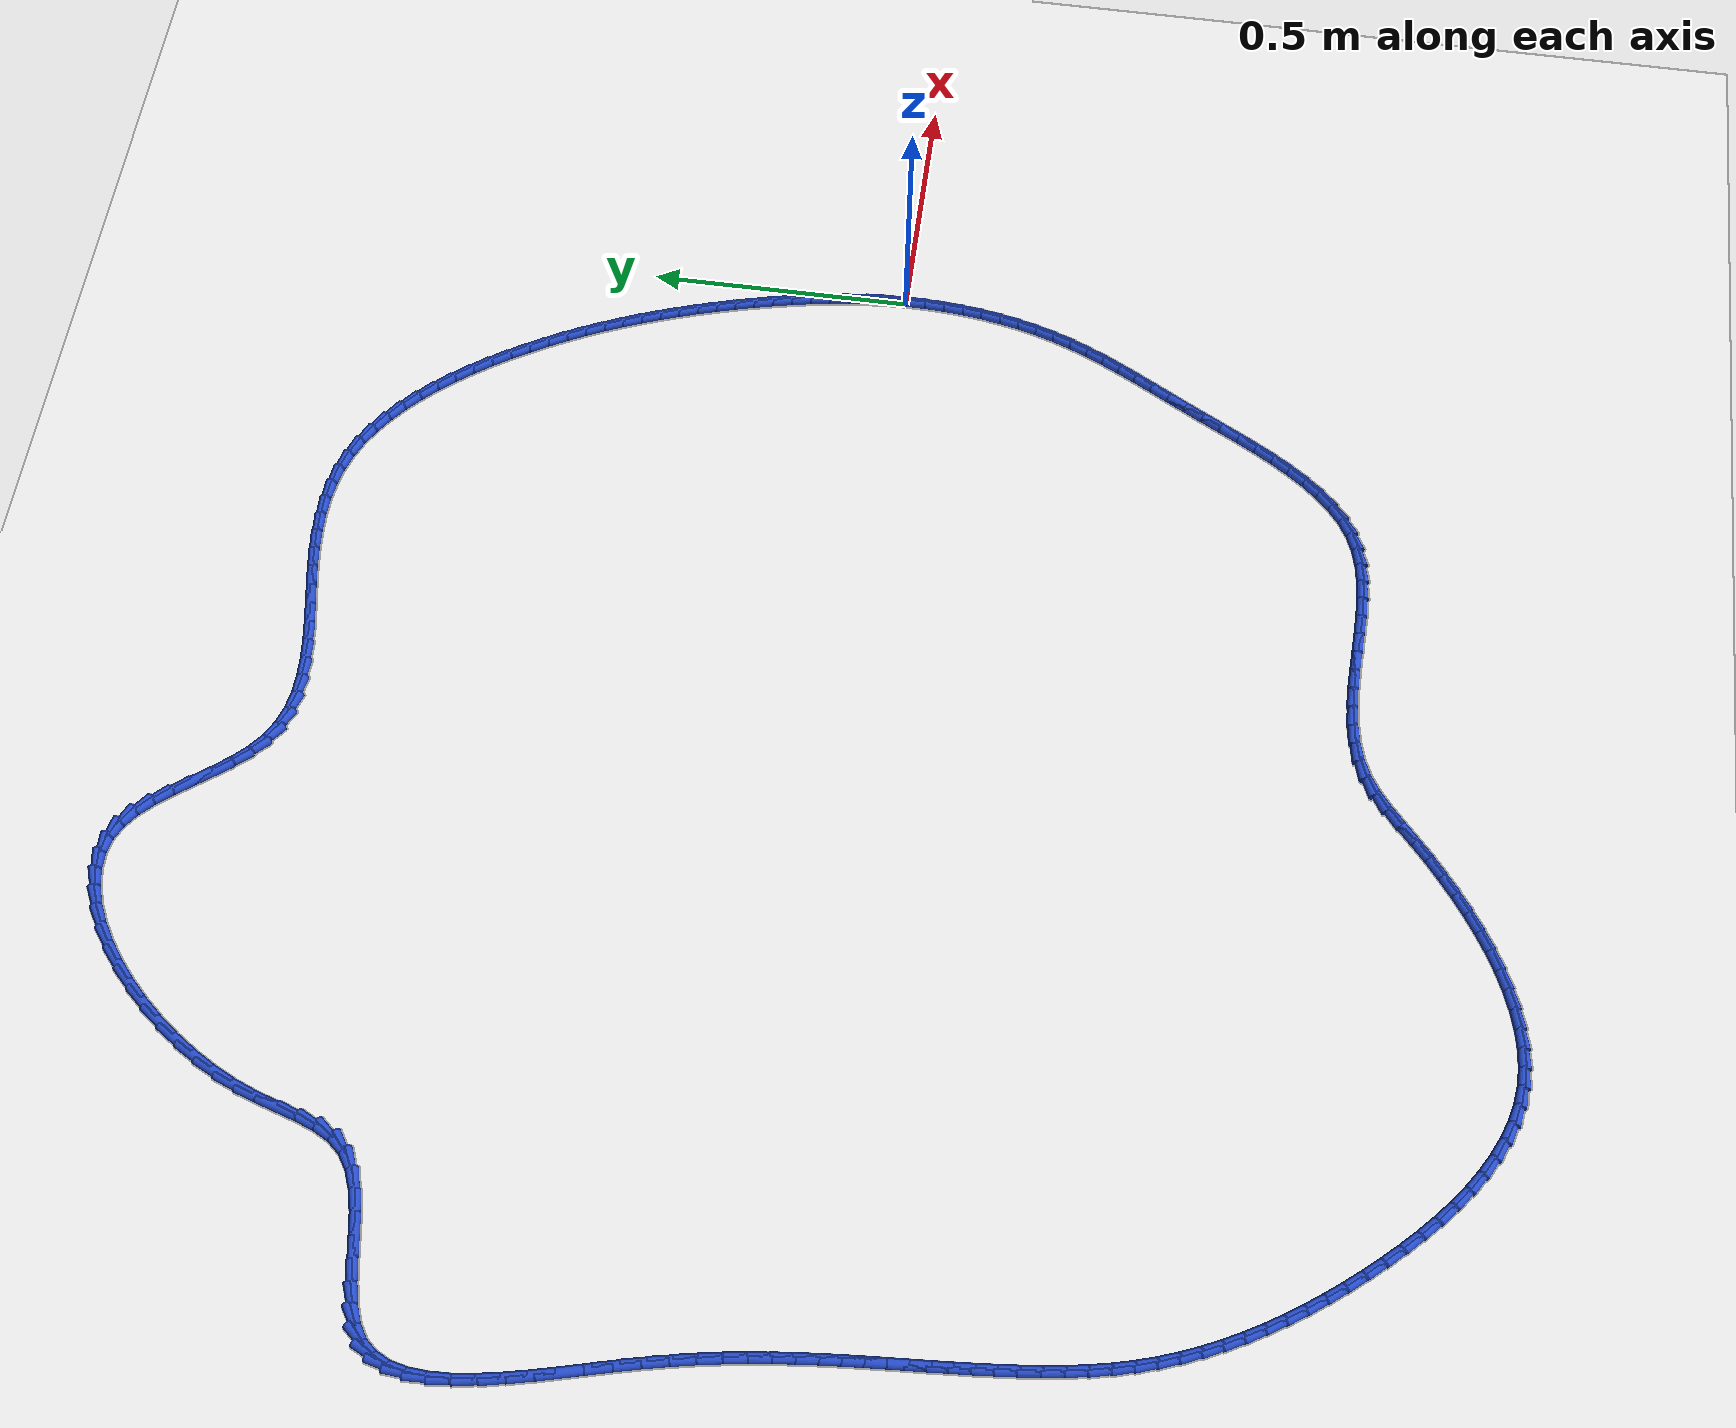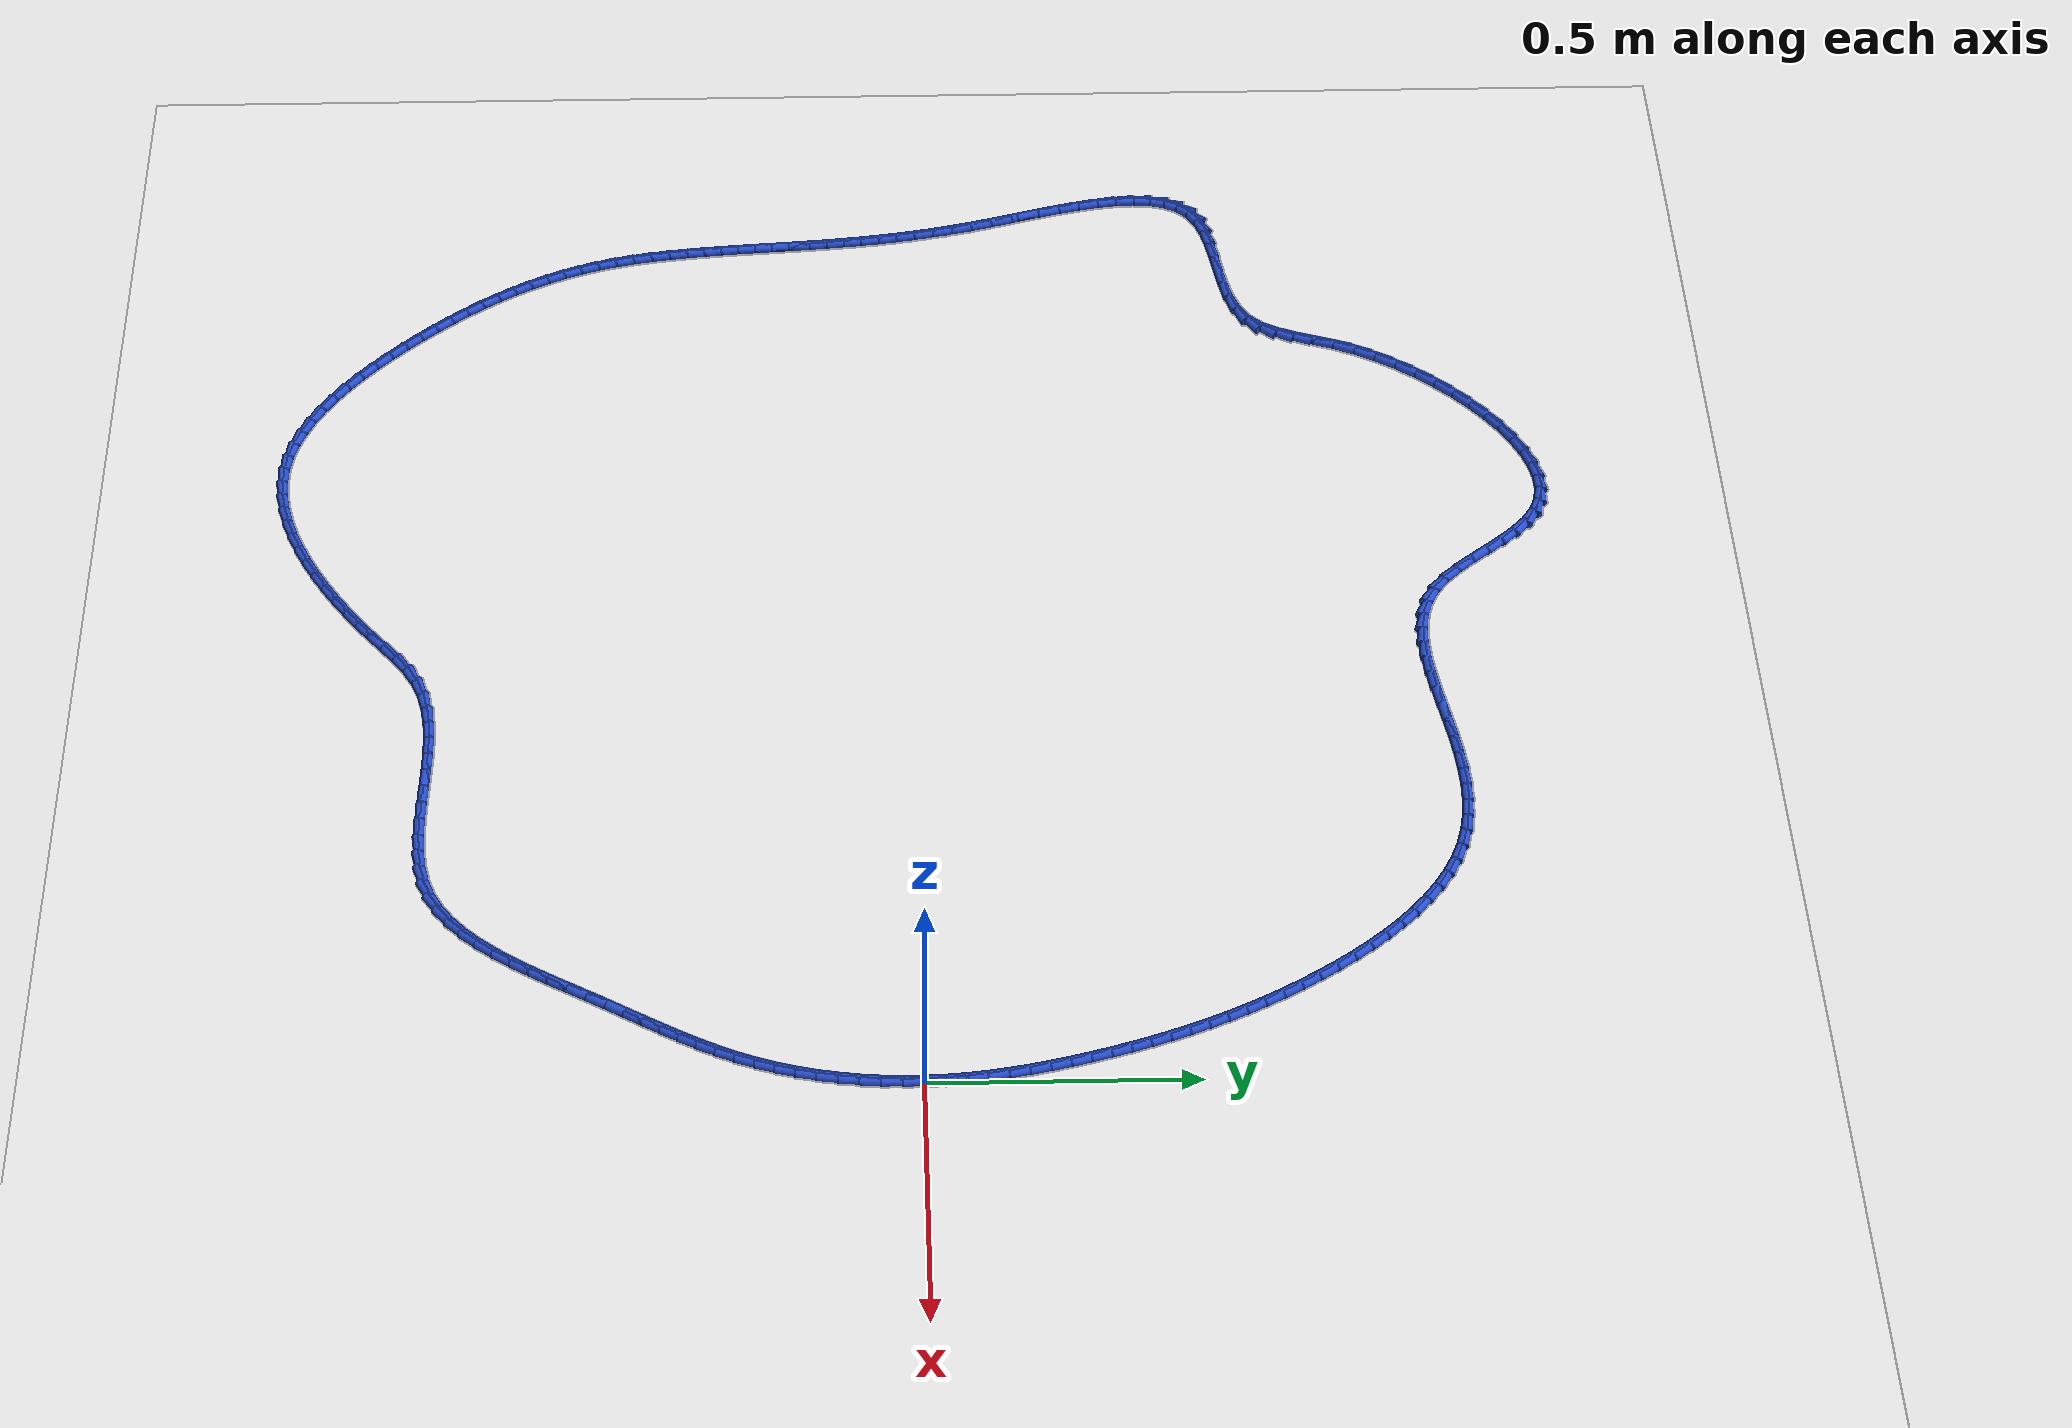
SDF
<sdf version="1.6">
 <world name="default">
  <light name="sun" type="directional">
   <pose>0 0 10 0 -0 0</pose>
   <diffuse>0.8 0.8 0.8 1</diffuse>
   <specular>0.2 0.2 0.2 1</specular>
   <attenuation>
    <range>1000</range>
    <constant>0.9</constant>
    <linear>0.01</linear>
    <quadratic>0.001</quadratic>
   </attenuation>
   <direction>-0.5 0.1 -0.9</direction>
  </light>
  <model name="ground_plane">
   <static>1</static>
   <link name="link">
    <collision name="collision">
     <geometry><plane><normal>0 0 1</normal><size>100 100</size></plane></geometry>
     <surface><friction><ode><mu>100</mu><mu2>50</mu2></ode></friction></surface>
    </collision>
    <visual name="visual">
     <cast_shadows>0</cast_shadows>
     <geometry><plane><normal>0 0 1</normal><size>100 100</size></plane></geometry>
     <material>
      <script><uri>file://media/materials/scripts/gazebo.material</uri><name>Gazebo/WhiteGlow</name></script>
     </material>
    </visual>
   </link>
  </model>
  <gravity>0 0 -9.8</gravity>
  <magnetic_field>6e-06 2.3e-05 -4.2e-05</magnetic_field>
  <atmosphere type="adiabatic"/>
  <physics name="default_physics" default="0" type="ode">
   <max_step_size>0.001</max_step_size>
   <real_time_factor>1</real_time_factor>
   <real_time_update_rate>1000</real_time_update_rate>
  </physics>
  <scene><ambient>0.4 0.4 0.4 1</ambient><background>0.7 0.7 0.7 1</background><shadows>1</shadows></scene>
  <spherical_coordinates>
   <surface_model>EARTH_WGS84</surface_model>
   <latitude_deg>0</latitude_deg>
   <longitude_deg>0</longitude_deg>
   <elevation>0</elevation>
   <heading_deg>0</heading_deg>
  </spherical_coordinates>
  <model name="line">
   <link name="link_0">
    <pose>1.6479873021779667e-17 4.163336342344337e-17 0.01 0 1.57 -1.5317288120726327</pose>
    <collision name="collision">
     <geometry><cylinder><radius>0.01</radius><length>0.08</length></cylinder></geometry>
    </collision>
    <visual name="visual">
     <material>
      <script><name>Gazebo/Blue</name><uri>file://media/materials/scripts/gazebo.material</uri></script>
     </material>
     <geometry><cylinder><radius>0.01</radius><length>0.08</length></cylinder></geometry>
    </visual>
   </link>
   <link name="link_1">
    <pose>-0.0014899844834011112 0.03811930134167298 0.01 0 1.57 -1.4931282186608994</pose>
    <collision name="collision">
     <geometry><cylinder><radius>0.01</radius><length>0.08</length></cylinder></geometry>
    </collision>
    <visual name="visual">
     <material>
      <script><name>Gazebo/Blue</name><uri>file://media/materials/scripts/gazebo.material</uri></script>
     </material>
     <geometry><cylinder><radius>0.01</radius><length>0.08</length></cylinder></geometry>
    </visual>
   </link>
   <link name="link_2">
    <pose>-0.004442782700830832 0.07606098006140873 0.01 0 1.57 -1.4574138592589685</pose>
    <collision name="collision">
     <geometry><cylinder><radius>0.01</radius><length>0.08</length></cylinder></geometry>
    </collision>
    <visual name="visual">
     <material>
      <script><name>Gazebo/Blue</name><uri>file://media/materials/scripts/gazebo.material</uri></script>
     </material>
     <geometry><cylinder><radius>0.01</radius><length>0.08</length></cylinder></geometry>
    </visual>
   </link>
   <link name="link_3">
    <pose>-0.008741418622784745 0.11381108126218124 0.01 0 1.57 -1.4246214544214557</pose>
    <collision name="collision">
     <geometry><cylinder><radius>0.01</radius><length>0.08</length></cylinder></geometry>
    </collision>
    <visual name="visual">
     <material>
      <script><name>Gazebo/Blue</name><uri>file://media/materials/scripts/gazebo.material</uri></script>
     </material>
     <geometry><cylinder><radius>0.01</radius><length>0.08</length></cylinder></geometry>
    </visual>
   </link>
   <link name="link_4">
    <pose>-0.014268916219758475 0.1513556500469646 0.01 0 1.57 -1.3947576710390879</pose>
    <collision name="collision">
     <geometry><cylinder><radius>0.01</radius><length>0.08</length></cylinder></geometry>
    </collision>
    <visual name="visual">
     <material>
      <script><name>Gazebo/Blue</name><uri>file://media/materials/scripts/gazebo.material</uri></script>
     </material>
     <geometry><cylinder><radius>0.01</radius><length>0.08</length></cylinder></geometry>
    </visual>
   </link>
   <link name="link_5">
    <pose>-0.020908299462247606 0.18868073151873274 0.01 0 1.57 -1.3678085568128728</pose>
    <collision name="collision">
     <geometry><cylinder><radius>0.01</radius><length>0.08</length></cylinder></geometry>
    </collision>
    <visual name="visual">
     <material>
      <script><name>Gazebo/Blue</name><uri>file://media/materials/scripts/gazebo.material</uri></script>
     </material>
     <geometry><cylinder><radius>0.01</radius><length>0.08</length></cylinder></geometry>
    </visual>
   </link>
   <link name="link_6">
    <pose>-0.028542592320747764 0.2257723707804597 0.01 0 1.57 -1.3437473016160464</pose>
    <collision name="collision">
     <geometry><cylinder><radius>0.01</radius><length>0.08</length></cylinder></geometry>
    </collision>
    <visual name="visual">
     <material>
      <script><name>Gazebo/Blue</name><uri>file://media/materials/scripts/gazebo.material</uri></script>
     </material>
     <geometry><cylinder><radius>0.01</radius><length>0.08</length></cylinder></geometry>
    </visual>
   </link>
   <link name="link_7">
    <pose>-0.037054818765754546 0.2626166129351194 0.01 0 1.57 -1.3225411309745525</pose>
    <collision name="collision">
     <geometry><cylinder><radius>0.01</radius><length>0.08</length></cylinder></geometry>
    </collision>
    <visual name="visual">
     <material>
      <script><name>Gazebo/Blue</name><uri>file://media/materials/scripts/gazebo.material</uri></script>
     </material>
     <geometry><cylinder><radius>0.01</radius><length>0.08</length></cylinder></geometry>
    </visual>
   </link>
   <link name="link_8">
    <pose>-0.046328002767763554 0.29919950308568594 0.01 0 1.57 -1.3038874209098905</pose>
    <collision name="collision">
     <geometry><cylinder><radius>0.01</radius><length>0.08</length></cylinder></geometry>
    </collision>
    <visual name="visual">
     <material>
      <script><name>Gazebo/Blue</name><uri>file://media/materials/scripts/gazebo.material</uri></script>
     </material>
     <geometry><cylinder><radius>0.01</radius><length>0.08</length></cylinder></geometry>
    </visual>
   </link>
   <link name="link_9">
    <pose>-0.05625606618419826 0.33550843181452994 0.01 0 1.57 -1.2852633298243463</pose>
    <collision name="collision">
     <geometry><cylinder><radius>0.01</radius><length>0.08</length></cylinder></geometry>
    </collision>
    <visual name="visual">
     <material>
      <script><name>Gazebo/Blue</name><uri>file://media/materials/scripts/gazebo.material</uri></script>
     </material>
     <geometry><cylinder><radius>0.01</radius><length>0.08</length></cylinder></geometry>
    </visual>
   </link>
   <link name="link_10">
    <pose>-0.06683426181227448 0.37154330026617244 0.01 0 1.57 -1.2653336064454472</pose>
    <collision name="collision">
     <geometry><cylinder><radius>0.01</radius><length>0.08</length></cylinder></geometry>
    </collision>
    <visual name="visual">
     <material>
      <script><name>Gazebo/Blue</name><uri>file://media/materials/scripts/gazebo.material</uri></script>
     </material>
     <geometry><cylinder><radius>0.01</radius><length>0.08</length></cylinder></geometry>
    </visual>
   </link>
   <link name="link_11">
    <pose>-0.078112896978811 0.40731080675010406 0.01 0 1.57 -1.2441290904263362</pose>
    <collision name="collision">
     <geometry><cylinder><radius>0.01</radius><length>0.08</length></cylinder></geometry>
    </collision>
    <visual name="visual">
     <material>
      <script><name>Gazebo/Blue</name><uri>file://media/materials/scripts/gazebo.material</uri></script>
     </material>
     <geometry><cylinder><radius>0.01</radius><length>0.08</length></cylinder></geometry>
    </visual>
   </link>
   <link name="link_12">
    <pose>-0.09014282735369664 0.44281771727557295 0.01 0 1.57 -1.2217051966672394</pose>
    <collision name="collision">
     <geometry><cylinder><radius>0.01</radius><length>0.08</length></cylinder></geometry>
    </collision>
    <visual name="visual">
     <material>
      <script><name>Gazebo/Blue</name><uri>file://media/materials/scripts/gazebo.material</uri></script>
     </material>
     <geometry><cylinder><radius>0.01</radius><length>0.08</length></cylinder></geometry>
    </visual>
   </link>
   <link name="link_13">
    <pose>-0.10297490860682014 0.4780707978518275 0.01 0 1.57 -1.1981286835815574</pose>
    <collision name="collision">
     <geometry><cylinder><radius>0.01</radius><length>0.08</length></cylinder></geometry>
    </collision>
    <visual name="visual">
     <material>
      <script><name>Gazebo/Blue</name><uri>file://media/materials/scripts/gazebo.material</uri></script>
     </material>
     <geometry><cylinder><radius>0.01</radius><length>0.08</length></cylinder></geometry>
    </visual>
   </link>
   <link name="link_14">
    <pose>-0.11665999640807029 0.5130768144881156 0.01 0 1.57 -1.1734777234963374</pose>
    <collision name="collision">
     <geometry><cylinder><radius>0.01</radius><length>0.08</length></cylinder></geometry>
    </collision>
    <visual name="visual">
     <material>
      <script><name>Gazebo/Blue</name><uri>file://media/materials/scripts/gazebo.material</uri></script>
     </material>
     <geometry><cylinder><radius>0.01</radius><length>0.08</length></cylinder></geometry>
    </visual>
   </link>
   <link name="link_15">
    <pose>-0.1312489464273358 0.5478425331936855 0.01 0 1.57 -1.147841650049137</pose>
    <collision name="collision">
     <geometry><cylinder><radius>0.01</radius><length>0.08</length></cylinder></geometry>
    </collision>
    <visual name="visual">
     <material>
      <script><name>Gazebo/Blue</name><uri>file://media/materials/scripts/gazebo.material</uri></script>
     </material>
     <geometry><cylinder><radius>0.01</radius><length>0.08</length></cylinder></geometry>
    </visual>
   </link>
   <link name="link_16">
    <pose>-0.14679261433450552 0.5823747199777852 0.01 0 1.57 -1.1213203472348447</pose>
    <collision name="collision">
     <geometry><cylinder><radius>0.01</radius><length>0.08</length></cylinder></geometry>
    </collision>
    <visual name="visual">
     <material>
      <script><name>Gazebo/Blue</name><uri>file://media/materials/scripts/gazebo.material</uri></script>
     </material>
     <geometry><cylinder><radius>0.01</radius><length>0.08</length></cylinder></geometry>
    </visual>
   </link>
   <link name="link_17">
    <pose>-0.1633418557994682 0.6166801408496633 0.01 0 1.57 -1.0940232627694966</pose>
    <collision name="collision">
     <geometry><cylinder><radius>0.01</radius><length>0.08</length></cylinder></geometry>
    </collision>
    <visual name="visual">
     <material>
      <script><name>Gazebo/Blue</name><uri>file://media/materials/scripts/gazebo.material</uri></script>
     </material>
     <geometry><cylinder><radius>0.01</radius><length>0.08</length></cylinder></geometry>
    </visual>
   </link>
   <link name="link_18">
    <pose>-0.18094752649211251 0.6507655618185675 0.01 0 1.57 -1.0660680508618456</pose>
    <collision name="collision">
     <geometry><cylinder><radius>0.01</radius><length>0.08</length></cylinder></geometry>
    </collision>
    <visual name="visual">
     <material>
      <script><name>Gazebo/Blue</name><uri>file://media/materials/scripts/gazebo.material</uri></script>
     </material>
     <geometry><cylinder><radius>0.01</radius><length>0.08</length></cylinder></geometry>
    </visual>
   </link>
   <link name="link_19">
    <pose>-0.19966048208232734 0.6846377488937464 0.01 0 1.57 -1.0375788745526946</pose>
    <collision name="collision">
     <geometry><cylinder><radius>0.01</radius><length>0.08</length></cylinder></geometry>
    </collision>
    <visual name="visual">
     <material>
      <script><name>Gazebo/Blue</name><uri>file://media/materials/scripts/gazebo.material</uri></script>
     </material>
     <geometry><cylinder><radius>0.01</radius><length>0.08</length></cylinder></geometry>
    </visual>
   </link>
   <link name="link_20">
    <pose>-0.21953157824000144 0.7183034680844478 0.01 0 1.57 -1.0085281038988079</pose>
    <collision name="collision">
     <geometry><cylinder><radius>0.01</radius><length>0.08</length></cylinder></geometry>
    </collision>
    <visual name="visual">
     <material>
      <script><name>Gazebo/Blue</name><uri>file://media/materials/scripts/gazebo.material</uri></script>
     </material>
     <geometry><cylinder><radius>0.01</radius><length>0.08</length></cylinder></geometry>
    </visual>
   </link>
   <link name="link_21">
    <pose>-0.2406095187670032 0.7517544728539155 0.01 0 1.57 -0.9769376198959406</pose>
    <collision name="collision">
     <geometry><cylinder><radius>0.01</radius><length>0.08</length></cylinder></geometry>
    </collision>
    <visual name="visual">
     <material>
      <script><name>Gazebo/Blue</name><uri>file://media/materials/scripts/gazebo.material</uri></script>
     </material>
     <geometry><cylinder><radius>0.01</radius><length>0.08</length></cylinder></geometry>
    </visual>
   </link>
   <link name="link_22">
    <pose>-0.26291586237252823 0.7847931384374061 0.01 0 1.57 -0.9410390834616802</pose>
    <collision name="collision">
     <geometry><cylinder><radius>0.01</radius><length>0.08</length></cylinder></geometry>
    </collision>
    <visual name="visual">
     <material>
      <script><name>Gazebo/Blue</name><uri>file://media/materials/scripts/gazebo.material</uri></script>
     </material>
     <geometry><cylinder><radius>0.01</radius><length>0.08</length></cylinder></geometry>
    </visual>
   </link>
   <link name="link_23">
    <pose>-0.2864535874889766 0.8170922144344327 0.01 0 1.57 -0.9002093344930429</pose>
    <collision name="collision">
     <geometry><cylinder><radius>0.01</radius><length>0.08</length></cylinder></geometry>
    </collision>
    <visual name="visual">
     <material>
      <script><name>Gazebo/Blue</name><uri>file://media/materials/scripts/gazebo.material</uri></script>
     </material>
     <geometry><cylinder><radius>0.01</radius><length>0.08</length></cylinder></geometry>
    </visual>
   </link>
   <link name="link_24">
    <pose>-0.31122531119113567 0.8483219294266147 0.01 0 1.57 -0.8537427876005834</pose>
    <collision name="collision">
     <geometry><cylinder><radius>0.01</radius><length>0.08</length></cylinder></geometry>
    </collision>
    <visual name="visual">
     <material>
      <script><name>Gazebo/Blue</name><uri>file://media/materials/scripts/gazebo.material</uri></script>
     </material>
     <geometry><cylinder><radius>0.01</radius><length>0.08</length></cylinder></geometry>
    </visual>
   </link>
   <link name="link_25">
    <pose>-0.337233650553793 0.8781525119955721 0.01 0 1.57 -0.8008281616777726</pose>
    <collision name="collision">
     <geometry><cylinder><radius>0.01</radius><length>0.08</length></cylinder></geometry>
    </collision>
    <visual name="visual">
     <material>
      <script><name>Gazebo/Blue</name><uri>file://media/materials/scripts/gazebo.material</uri></script>
     </material>
     <geometry><cylinder><radius>0.01</radius><length>0.08</length></cylinder></geometry>
    </visual>
   </link>
   <link name="link_26">
    <pose>-0.3644812226517359 0.9062541907229245 0.01 0 1.57 -0.7405665021716514</pose>
    <collision name="collision">
     <geometry><cylinder><radius>0.01</radius><length>0.08</length></cylinder></geometry>
    </collision>
    <visual name="visual">
     <material>
      <script><name>Gazebo/Blue</name><uri>file://media/materials/scripts/gazebo.material</uri></script>
     </material>
     <geometry><cylinder><radius>0.01</radius><length>0.08</length></cylinder></geometry>
    </visual>
   </link>
   <link name="link_27">
    <pose>-0.39297064455975206 0.9322971941902918 0.01 0 1.57 -0.6720167203840954</pose>
    <collision name="collision">
     <geometry><cylinder><radius>0.01</radius><length>0.08</length></cylinder></geometry>
    </collision>
    <visual name="visual">
     <material>
      <script><name>Gazebo/Blue</name><uri>file://media/materials/scripts/gazebo.material</uri></script>
     </material>
     <geometry><cylinder><radius>0.01</radius><length>0.08</length></cylinder></geometry>
    </visual>
   </link>
   <link name="link_28">
    <pose>-0.4227045333526288 0.9559517509792936 0.01 0 1.57 -0.5942857002543495</pose>
    <collision name="collision">
     <geometry><cylinder><radius>0.01</radius><length>0.08</length></cylinder></geometry>
    </collision>
    <visual name="visual">
     <material>
      <script><name>Gazebo/Blue</name><uri>file://media/materials/scripts/gazebo.material</uri></script>
     </material>
     <geometry><cylinder><radius>0.01</radius><length>0.08</length></cylinder></geometry>
    </visual>
   </link>
   <link name="link_29">
    <pose>-0.45368550610515335 0.9768880896715495 0.01 0 1.57 -0.5066815902784058</pose>
    <collision name="collision">
     <geometry><cylinder><radius>0.01</radius><length>0.08</length></cylinder></geometry>
    </collision>
    <visual name="visual">
     <material>
      <script><name>Gazebo/Blue</name><uri>file://media/materials/scripts/gazebo.material</uri></script>
     </material>
     <geometry><cylinder><radius>0.01</radius><length>0.08</length></cylinder></geometry>
    </visual>
   </link>
   <link name="link_30">
    <pose>-0.48591617989211366 0.9947764388486795 0.01 0 1.57 -0.408940308850533</pose>
    <collision name="collision">
     <geometry><cylinder><radius>0.01</radius><length>0.08</length></cylinder></geometry>
    </collision>
    <visual name="visual">
     <material>
      <script><name>Gazebo/Blue</name><uri>file://media/materials/scripts/gazebo.material</uri></script>
     </material>
     <geometry><cylinder><radius>0.01</radius><length>0.08</length></cylinder></geometry>
    </visual>
   </link>
   <link name="link_31">
    <pose>-0.5193991717882966 1.0092870270923027 0.01 0 1.57 -0.30239859048190465</pose>
    <collision name="collision">
     <geometry><cylinder><radius>0.01</radius><length>0.08</length></cylinder></geometry>
    </collision>
    <visual name="visual">
     <material>
      <script><name>Gazebo/Blue</name><uri>file://media/materials/scripts/gazebo.material</uri></script>
     </material>
     <geometry><cylinder><radius>0.01</radius><length>0.08</length></cylinder></geometry>
    </visual>
   </link>
   <link name="link_32">
    <pose>-0.554131824338189 1.020122444721563 0.01 0 1.57 -0.1991836640475621</pose>
    <collision name="collision">
     <geometry><cylinder><radius>0.01</radius><length>0.08</length></cylinder></geometry>
    </collision>
    <visual name="visual">
     <material>
      <script><name>Gazebo/Blue</name><uri>file://media/materials/scripts/gazebo.material</uri></script>
     </material>
     <geometry><cylinder><radius>0.01</radius><length>0.08</length></cylinder></geometry>
    </visual>
   </link>
   <link name="link_33">
    <pose>-0.5900483578545886 1.0273725667951425 0.01 0 1.57 -0.10797520691942922</pose>
    <collision name="collision">
     <geometry><cylinder><radius>0.01</radius><length>0.08</length></cylinder></geometry>
    </collision>
    <visual name="visual">
     <material>
      <script><name>Gazebo/Blue</name><uri>file://media/materials/scripts/gazebo.material</uri></script>
     </material>
     <geometry><cylinder><radius>0.01</radius><length>0.08</length></cylinder></geometry>
    </visual>
   </link>
   <link name="link_34">
    <pose>-0.6270413944280164 1.0313824931356246 0.01 0 1.57 -0.029477488322569353</pose>
    <collision name="collision">
     <geometry><cylinder><radius>0.01</radius><length>0.08</length></cylinder></geometry>
    </collision>
    <visual name="visual">
     <material>
      <script><name>Gazebo/Blue</name><uri>file://media/materials/scripts/gazebo.material</uri></script>
     </material>
     <geometry><cylinder><radius>0.01</radius><length>0.08</length></cylinder></geometry>
    </visual>
   </link>
   <link name="link_35">
    <pose>-0.6650028224899194 1.0325018249109297 0.01 0 1.57 0.03660391834432339</pose>
    <collision name="collision">
     <geometry><cylinder><radius>0.01</radius><length>0.08</length></cylinder></geometry>
    </collision>
    <visual name="visual">
     <material>
      <script><name>Gazebo/Blue</name><uri>file://media/materials/scripts/gazebo.material</uri></script>
     </material>
     <geometry><cylinder><radius>0.01</radius><length>0.08</length></cylinder></geometry>
    </visual>
   </link>
   <link name="link_36">
    <pose>-0.703824530471745 1.0310801632889777 0.01 0 1.57 0.09104654951064257</pose>
    <collision name="collision">
     <geometry><cylinder><radius>0.01</radius><length>0.08</length></cylinder></geometry>
    </collision>
    <visual name="visual">
     <material>
      <script><name>Gazebo/Blue</name><uri>file://media/materials/scripts/gazebo.material</uri></script>
     </material>
     <geometry><cylinder><radius>0.01</radius><length>0.08</length></cylinder></geometry>
    </visual>
   </link>
   <link name="link_37">
    <pose>-0.7433984068049408 1.0274671094376884 0.01 0 1.57 0.1347586860136338</pose>
    <collision name="collision">
     <geometry><cylinder><radius>0.01</radius><length>0.08</length></cylinder></geometry>
    </collision>
    <visual name="visual">
     <material>
      <script><name>Gazebo/Blue</name><uri>file://media/materials/scripts/gazebo.material</uri></script>
     </material>
     <geometry><cylinder><radius>0.01</radius><length>0.08</length></cylinder></geometry>
    </visual>
   </link>
   <link name="link_38">
    <pose>-0.7836153436980116 1.0220144814383636 0.01 0 1.57 0.1652870612479473</pose>
    <collision name="collision">
     <geometry><cylinder><radius>0.01</radius><length>0.08</length></cylinder></geometry>
    </collision>
    <visual name="visual">
     <material>
      <script><name>Gazebo/Blue</name><uri>file://media/materials/scripts/gazebo.material</uri></script>
     </material>
     <geometry><cylinder><radius>0.01</radius><length>0.08</length></cylinder></geometry>
    </visual>
   </link>
   <link name="link_39">
    <pose>-0.8242968758614666 1.0152284398983111 0.01 0 1.57 0.17826257744224713</pose>
    <collision name="collision">
     <geometry><cylinder><radius>0.01</radius><length>0.08</length></cylinder></geometry>
    </collision>
    <visual name="visual">
     <material>
      <script><name>Gazebo/Blue</name><uri>file://media/materials/scripts/gazebo.material</uri></script>
     </material>
     <geometry><cylinder><radius>0.01</radius><length>0.08</length></cylinder></geometry>
    </visual>
   </link>
   <link name="link_40">
    <pose>-0.8651511277795053 1.007867519303795 0.01 0 1.57 0.17389211119052903</pose>
    <collision name="collision">
     <geometry><cylinder><radius>0.01</radius><length>0.08</length></cylinder></geometry>
    </collision>
    <visual name="visual">
     <material>
      <script><name>Gazebo/Blue</name><uri>file://media/materials/scripts/gazebo.material</uri></script>
     </material>
     <geometry><cylinder><radius>0.01</radius><length>0.08</length></cylinder></geometry>
    </visual>
   </link>
   <link name="link_41">
    <pose>-0.9058757437073567 1.0007135759888834 0.01 0 1.57 0.15183083544688275</pose>
    <collision name="collision">
     <geometry><cylinder><radius>0.01</radius><length>0.08</length></cylinder></geometry>
    </collision>
    <visual name="visual">
     <material>
      <script><name>Gazebo/Blue</name><uri>file://media/materials/scripts/gazebo.material</uri></script>
     </material>
     <geometry><cylinder><radius>0.01</radius><length>0.08</length></cylinder></geometry>
    </visual>
   </link>
   <link name="link_42">
    <pose>-0.9461683679002486 0.994548466287645 0.01 0 1.57 0.11063364046974347</pose>
    <collision name="collision">
     <geometry><cylinder><radius>0.01</radius><length>0.08</length></cylinder></geometry>
    </collision>
    <visual name="visual">
     <material>
      <script><name>Gazebo/Blue</name><uri>file://media/materials/scripts/gazebo.material</uri></script>
     </material>
     <geometry><cylinder><radius>0.01</radius><length>0.08</length></cylinder></geometry>
    </visual>
   </link>
   <link name="link_43">
    <pose>-0.9857266446134115 0.9901540465341484 0.01 0 1.57 0.04777768936960683</pose>
    <collision name="collision">
     <geometry><cylinder><radius>0.01</radius><length>0.08</length></cylinder></geometry>
    </collision>
    <visual name="visual">
     <material>
      <script><name>Gazebo/Blue</name><uri>file://media/materials/scripts/gazebo.material</uri></script>
     </material>
     <geometry><cylinder><radius>0.01</radius><length>0.08</length></cylinder></geometry>
    </visual>
   </link>
   <link name="link_44">
    <pose>-1.0242482181020733 0.9883121730624618 0.01 0 1.57 -0.040119080579638734</pose>
    <collision name="collision">
     <geometry><cylinder><radius>0.01</radius><length>0.08</length></cylinder></geometry>
    </collision>
    <visual name="visual">
     <material>
      <script><name>Gazebo/Blue</name><uri>file://media/materials/scripts/gazebo.material</uri></script>
     </material>
     <geometry><cylinder><radius>0.01</radius><length>0.08</length></cylinder></geometry>
    </visual>
   </link>
   <link name="link_45">
    <pose>-1.0614307326214631 0.9898047022066538 0.01 0 1.57 -0.15652049418129263</pose>
    <collision name="collision">
     <geometry><cylinder><radius>0.01</radius><length>0.08</length></cylinder></geometry>
    </collision>
    <visual name="visual">
     <material>
      <script><name>Gazebo/Blue</name><uri>file://media/materials/scripts/gazebo.material</uri></script>
     </material>
     <geometry><cylinder><radius>0.01</radius><length>0.08</length></cylinder></geometry>
    </visual>
   </link>
   <link name="link_46">
    <pose>-1.09697183242681 0.9954134903007933 0.01 0 1.57 -0.30309467864322426</pose>
    <collision name="collision">
     <geometry><cylinder><radius>0.01</radius><length>0.08</length></cylinder></geometry>
    </collision>
    <visual name="visual">
     <material>
      <script><name>Gazebo/Blue</name><uri>file://media/materials/scripts/gazebo.material</uri></script>
     </material>
     <geometry><cylinder><radius>0.01</radius><length>0.08</length></cylinder></geometry>
    </visual>
   </link>
   <link name="link_47">
    <pose>-1.1305691617733429 1.0059203936789487 0.01 0 1.57 -0.47660868017897223</pose>
    <collision name="collision">
     <geometry><cylinder><radius>0.01</radius><length>0.08</length></cylinder></geometry>
    </collision>
    <visual name="visual">
     <material>
      <script><name>Gazebo/Blue</name><uri>file://media/materials/scripts/gazebo.material</uri></script>
     </material>
     <geometry><cylinder><radius>0.01</radius><length>0.08</length></cylinder></geometry>
    </visual>
   </link>
   <link name="link_48">
    <pose>-1.1619203649162904 1.0221072686751886 0.01 0 1.57 -0.6577895668542895</pose>
    <collision name="collision">
     <geometry><cylinder><radius>0.01</radius><length>0.08</length></cylinder></geometry>
    </collision>
    <visual name="visual">
     <material>
      <script><name>Gazebo/Blue</name><uri>file://media/materials/scripts/gazebo.material</uri></script>
     </material>
     <geometry><cylinder><radius>0.01</radius><length>0.08</length></cylinder></geometry>
    </visual>
   </link>
   <link name="link_49">
    <pose>-1.1908352684853498 1.0444460299907152 0.01 0 1.57 -0.7926781146108255</pose>
    <collision name="collision">
     <geometry><cylinder><radius>0.01</radius><length>0.08</length></cylinder></geometry>
    </collision>
    <visual name="visual">
     <material>
      <script><name>Gazebo/Blue</name><uri>file://media/materials/scripts/gazebo.material</uri></script>
     </material>
     <geometry><cylinder><radius>0.01</radius><length>0.08</length></cylinder></geometry>
    </visual>
   </link>
   <link name="link_50">
    <pose>-1.2177295385535447 1.0717347565997681 0.01 0 1.57 -0.8741696562402795</pose>
    <collision name="collision">
     <geometry><cylinder><radius>0.01</radius><length>0.08</length></cylinder></geometry>
    </collision>
    <visual name="visual">
     <material>
      <script><name>Gazebo/Blue</name><uri>file://media/materials/scripts/gazebo.material</uri></script>
     </material>
     <geometry><cylinder><radius>0.01</radius><length>0.08</length></cylinder></geometry>
    </visual>
   </link>
   <link name="link_51">
    <pose>-1.2432224340740237 1.1022090335018886 0.01 0 1.57 -0.9116368911753141</pose>
    <collision name="collision">
     <geometry><cylinder><radius>0.01</radius><length>0.08</length></cylinder></geometry>
    </collision>
    <visual name="visual">
     <material>
      <script><name>Gazebo/Blue</name><uri>file://media/materials/scripts/gazebo.material</uri></script>
     </material>
     <geometry><cylinder><radius>0.01</radius><length>0.08</length></cylinder></geometry>
    </visual>
   </link>
   <link name="link_52">
    <pose>-1.267933365321975 1.1341040276184626 0.01 0 1.57 -0.9095792920194257</pose>
    <collision name="collision">
     <geometry><cylinder><radius>0.01</radius><length>0.08</length></cylinder></geometry>
    </collision>
    <visual name="visual">
     <material>
      <script><name>Gazebo/Blue</name><uri>file://media/materials/scripts/gazebo.material</uri></script>
     </material>
     <geometry><cylinder><radius>0.01</radius><length>0.08</length></cylinder></geometry>
    </visual>
   </link>
   <link name="link_53">
    <pose>-1.292481742572587 1.165654905870876 0.01 0 1.57 -0.8667047840840384</pose>
    <collision name="collision">
     <geometry><cylinder><radius>0.01</radius><length>0.08</length></cylinder></geometry>
    </collision>
    <visual name="visual">
     <material>
      <script><name>Gazebo/Blue</name><uri>file://media/materials/scripts/gazebo.material</uri></script>
     </material>
     <geometry><cylinder><radius>0.01</radius><length>0.08</length></cylinder></geometry>
    </visual>
   </link>
   <link name="link_54">
    <pose>-1.3174869761010477 1.1950968351805147 0.01 0 1.57 -0.7754593561392966</pose>
    <collision name="collision">
     <geometry><cylinder><radius>0.01</radius><length>0.08</length></cylinder></geometry>
    </collision>
    <visual name="visual">
     <material>
      <script><name>Gazebo/Blue</name><uri>file://media/materials/scripts/gazebo.material</uri></script>
     </material>
     <geometry><cylinder><radius>0.01</radius><length>0.08</length></cylinder></geometry>
    </visual>
   </link>
   <link name="link_55">
    <pose>-1.3435684761825448 1.2206649824687636 0.01 0 1.57 -0.6223605549805019</pose>
    <collision name="collision">
     <geometry><cylinder><radius>0.01</radius><length>0.08</length></cylinder></geometry>
    </collision>
    <visual name="visual">
     <material>
      <script><name>Gazebo/Blue</name><uri>file://media/materials/scripts/gazebo.material</uri></script>
     </material>
     <geometry><cylinder><radius>0.01</radius><length>0.08</length></cylinder></geometry>
    </visual>
   </link>
   <link name="link_56">
    <pose>-1.371345653092268 1.2405945146570099 0.01 0 1.57 -0.4054876587730237</pose>
    <collision name="collision">
     <geometry><cylinder><radius>0.01</radius><length>0.08</length></cylinder></geometry>
    </collision>
    <visual name="visual">
     <material>
      <script><name>Gazebo/Blue</name><uri>file://media/materials/scripts/gazebo.material</uri></script>
     </material>
     <geometry><cylinder><radius>0.01</radius><length>0.08</length></cylinder></geometry>
    </visual>
   </link>
   <link name="link_57">
    <pose>-1.4012883910001843 1.2534482411803511 0.01 0 1.57 -0.18110048506655507</pose>
    <collision name="collision">
     <geometry><cylinder><radius>0.01</radius><length>0.08</length></cylinder></geometry>
    </collision>
    <visual name="visual">
     <material>
      <script><name>Gazebo/Blue</name><uri>file://media/materials/scripts/gazebo.material</uri></script>
     </material>
     <geometry><cylinder><radius>0.01</radius><length>0.08</length></cylinder></geometry>
    </visual>
   </link>
   <link name="link_58">
    <pose>-1.4331823538902666 1.2592882389184827 0.01 0 1.57 0.020426566300501093</pose>
    <collision name="collision">
     <geometry><cylinder><radius>0.01</radius><length>0.08</length></cylinder></geometry>
    </collision>
    <visual name="visual">
     <material>
      <script><name>Gazebo/Blue</name><uri>file://media/materials/scripts/gazebo.material</uri></script>
     </material>
     <geometry><cylinder><radius>0.01</radius><length>0.08</length></cylinder></geometry>
    </visual>
   </link>
   <link name="link_59">
    <pose>-1.4666176094955612 1.2586051764490662 0.01 0 1.57 0.19188457313150134</pose>
    <collision name="collision">
     <geometry><cylinder><radius>0.01</radius><length>0.08</length></cylinder></geometry>
    </collision>
    <visual name="visual">
     <material>
      <script><name>Gazebo/Blue</name><uri>file://media/materials/scripts/gazebo.material</uri></script>
     </material>
     <geometry><cylinder><radius>0.01</radius><length>0.08</length></cylinder></geometry>
    </visual>
   </link>
   <link name="link_60">
    <pose>-1.501184210137573 1.2518897561196243 0.01 0 1.57 0.3343067527025954</pose>
    <collision name="collision">
     <geometry><cylinder><radius>0.01</radius><length>0.08</length></cylinder></geometry>
    </collision>
    <visual name="visual">
     <material>
      <script><name>Gazebo/Blue</name><uri>file://media/materials/scripts/gazebo.material</uri></script>
     </material>
     <geometry><cylinder><radius>0.01</radius><length>0.08</length></cylinder></geometry>
    </visual>
   </link>
   <link name="link_61">
    <pose>-1.536472208137808 1.2396326802776796 0.01 0 1.57 0.45253718787691133</pose>
    <collision name="collision">
     <geometry><cylinder><radius>0.01</radius><length>0.08</length></cylinder></geometry>
    </collision>
    <visual name="visual">
     <material>
      <script><name>Gazebo/Blue</name><uri>file://media/materials/scripts/gazebo.material</uri></script>
     </material>
     <geometry><cylinder><radius>0.01</radius><length>0.08</length></cylinder></geometry>
    </visual>
   </link>
   <link name="link_62">
    <pose>-1.5720716558177714 1.2223246512707548 0.01 0 1.57 0.5520949801280083</pose>
    <collision name="collision">
     <geometry><cylinder><radius>0.01</radius><length>0.08</length></cylinder></geometry>
    </collision>
    <visual name="visual">
     <material>
      <script><name>Gazebo/Blue</name><uri>file://media/materials/scripts/gazebo.material</uri></script>
     </material>
     <geometry><cylinder><radius>0.01</radius><length>0.08</length></cylinder></geometry>
    </visual>
   </link>
   <link name="link_63">
    <pose>-1.6075726054989683 1.2004563714463732 0.01 0 1.57 0.637870811399206</pose>
    <collision name="collision">
     <geometry><cylinder><radius>0.01</radius><length>0.08</length></cylinder></geometry>
    </collision>
    <visual name="visual">
     <material>
      <script><name>Gazebo/Blue</name><uri>file://media/materials/scripts/gazebo.material</uri></script>
     </material>
     <geometry><cylinder><radius>0.01</radius><length>0.08</length></cylinder></geometry>
    </visual>
   </link>
   <link name="link_64">
    <pose>-1.6425651095029041 1.174518543152058 0.01 0 1.57 0.7138523041166956</pose>
    <collision name="collision">
     <geometry><cylinder><radius>0.01</radius><length>0.08</length></cylinder></geometry>
    </collision>
    <visual name="visual">
     <material>
      <script><name>Gazebo/Blue</name><uri>file://media/materials/scripts/gazebo.material</uri></script>
     </material>
     <geometry><cylinder><radius>0.01</radius><length>0.08</length></cylinder></geometry>
    </visual>
   </link>
   <link name="link_65">
    <pose>-1.6766392201510851 1.1450018687353314 0.01 0 1.57 0.7832413166347811</pose>
    <collision name="collision">
     <geometry><cylinder><radius>0.01</radius><length>0.08</length></cylinder></geometry>
    </collision>
    <visual name="visual">
     <material>
      <script><name>Gazebo/Blue</name><uri>file://media/materials/scripts/gazebo.material</uri></script>
     </material>
     <geometry><cylinder><radius>0.01</radius><length>0.08</length></cylinder></geometry>
    </visual>
   </link>
   <link name="link_66">
    <pose>-1.7093849897650153 1.1123970505437162 0.01 0 1.57 0.8486695127289309</pose>
    <collision name="collision">
     <geometry><cylinder><radius>0.01</radius><length>0.08</length></cylinder></geometry>
    </collision>
    <visual name="visual">
     <material>
      <script><name>Gazebo/Blue</name><uri>file://media/materials/scripts/gazebo.material</uri></script>
     </material>
     <geometry><cylinder><radius>0.01</radius><length>0.08</length></cylinder></geometry>
    </visual>
   </link>
   <link name="link_67">
    <pose>-1.740392470666201 1.0771947909247357 0.01 0 1.57 0.9124117640541846</pose>
    <collision name="collision">
     <geometry><cylinder><radius>0.01</radius><length>0.08</length></cylinder></geometry>
    </collision>
    <visual name="visual">
     <material>
      <script><name>Gazebo/Blue</name><uri>file://media/materials/scripts/gazebo.material</uri></script>
     </material>
     <geometry><cylinder><radius>0.01</radius><length>0.08</length></cylinder></geometry>
    </visual>
   </link>
   <link name="link_68">
    <pose>-1.7692517151761478 1.0398857922259128 0.01 0 1.57 0.9765762587988626</pose>
    <collision name="collision">
     <geometry><cylinder><radius>0.01</radius><length>0.08</length></cylinder></geometry>
    </collision>
    <visual name="visual">
     <material>
      <script><name>Gazebo/Blue</name><uri>file://media/materials/scripts/gazebo.material</uri></script>
     </material>
     <geometry><cylinder><radius>0.01</radius><length>0.08</length></cylinder></geometry>
    </visual>
   </link>
   <link name="link_69">
    <pose>-1.79555277561636 1.0009607567947698 0.01 0 1.57 1.0432769722912378</pose>
    <collision name="collision">
     <geometry><cylinder><radius>0.01</radius><length>0.08</length></cylinder></geometry>
    </collision>
    <visual name="visual">
     <material>
      <script><name>Gazebo/Blue</name><uri>file://media/materials/scripts/gazebo.material</uri></script>
     </material>
     <geometry><cylinder><radius>0.01</radius><length>0.08</length></cylinder></geometry>
    </visual>
   </link>
   <link name="link_70">
    <pose>-1.8188857043083444 0.9609103869788304 0.01 0 1.57 1.1148002284520568</pose>
    <collision name="collision">
     <geometry><cylinder><radius>0.01</radius><length>0.08</length></cylinder></geometry>
    </collision>
    <visual name="visual">
     <material>
      <script><name>Gazebo/Blue</name><uri>file://media/materials/scripts/gazebo.material</uri></script>
     </material>
     <geometry><cylinder><radius>0.01</radius><length>0.08</length></cylinder></geometry>
    </visual>
   </link>
   <link name="link_71">
    <pose>-1.838840553573605 0.920225385125617 0.01 0 1.57 1.1932738534176512</pose>
    <collision name="collision">
     <geometry><cylinder><radius>0.01</radius><length>0.08</length></cylinder></geometry>
    </collision>
    <visual name="visual">
     <material>
      <script><name>Gazebo/Blue</name><uri>file://media/materials/scripts/gazebo.material</uri></script>
     </material>
     <geometry><cylinder><radius>0.01</radius><length>0.08</length></cylinder></geometry>
    </visual>
   </link>
   <link name="link_72">
    <pose>-1.8550285310523795 0.879402608929121 0.01 0 1.57 1.256429184824553</pose>
    <collision name="collision">
     <geometry><cylinder><radius>0.01</radius><length>0.08</length></cylinder></geometry>
    </collision>
    <visual name="visual">
     <material>
      <script><name>Gazebo/Blue</name><uri>file://media/materials/scripts/gazebo.material</uri></script>
     </material>
     <geometry><cylinder><radius>0.01</radius><length>0.08</length></cylinder></geometry>
    </visual>
   </link>
   <link name="link_73">
    <pose>-1.868088098159212 0.839237805595352 0.01 0 1.57 1.2661865175130402</pose>
    <collision name="collision">
     <geometry><cylinder><radius>0.01</radius><length>0.08</length></cylinder></geometry>
    </collision>
    <visual name="visual">
     <material>
      <script><name>Gazebo/Blue</name><uri>file://media/materials/scripts/gazebo.material</uri></script>
     </material>
     <geometry><cylinder><radius>0.01</radius><length>0.08</length></cylinder></geometry>
    </visual>
   </link>
   <link name="link_74">
    <pose>-1.8801244733007618 0.8009534895932732 0.01 0 1.57 1.2107726769507565</pose>
    <collision name="collision">
     <geometry><cylinder><radius>0.01</radius><length>0.08</length></cylinder></geometry>
    </collision>
    <visual name="visual">
     <material>
      <script><name>Gazebo/Blue</name><uri>file://media/materials/scripts/gazebo.material</uri></script>
     </material>
     <geometry><cylinder><radius>0.01</radius><length>0.08</length></cylinder></geometry>
    </visual>
   </link>
   <link name="link_75">
    <pose>-1.893355441273737 0.7658049276817241 0.01 0 1.57 1.0748007293436144</pose>
    <collision name="collision">
     <geometry><cylinder><radius>0.01</radius><length>0.08</length></cylinder></geometry>
    </collision>
    <visual name="visual">
     <material>
      <script><name>Gazebo/Blue</name><uri>file://media/materials/scripts/gazebo.material</uri></script>
     </material>
     <geometry><cylinder><radius>0.01</radius><length>0.08</length></cylinder></geometry>
    </visual>
   </link>
   <link name="link_76">
    <pose>-1.9099987868748478 0.7350473866195439 0.01 0 1.57 0.8452651993104219</pose>
    <collision name="collision">
     <geometry><cylinder><radius>0.01</radius><length>0.08</length></cylinder></geometry>
    </collision>
    <visual name="visual">
     <material>
      <script><name>Gazebo/Blue</name><uri>file://media/materials/scripts/gazebo.material</uri></script>
     </material>
     <geometry><cylinder><radius>0.01</radius><length>0.08</length></cylinder></geometry>
    </visual>
   </link>
   <link name="link_77">
    <pose>-1.9322708612131148 0.7099351607765856 0.01 0 1.57 0.5734886037261481</pose>
    <collision name="collision">
     <geometry><cylinder><radius>0.01</radius><length>0.08</length></cylinder></geometry>
    </collision>
    <visual name="visual">
     <material>
      <script><name>Gazebo/Blue</name><uri>file://media/materials/scripts/gazebo.material</uri></script>
     </material>
     <geometry><cylinder><radius>0.01</radius><length>0.08</length></cylinder></geometry>
    </visual>
   </link>
   <link name="link_78">
    <pose>-1.961451488005 0.6910873511468203 0.01 0 1.57 0.37471797323229117</pose>
    <collision name="collision">
     <geometry><cylinder><radius>0.01</radius><length>0.08</length></cylinder></geometry>
    </collision>
    <visual name="visual">
     <material>
      <script><name>Gazebo/Blue</name><uri>file://media/materials/scripts/gazebo.material</uri></script>
     </material>
     <geometry><cylinder><radius>0.01</radius><length>0.08</length></cylinder></geometry>
    </visual>
   </link>
   <link name="link_79">
    <pose>-1.996269994416055 0.6773932016722898 0.01 0 1.57 0.2511391753238968</pose>
    <collision name="collision">
     <geometry><cylinder><radius>0.01</radius><length>0.08</length></cylinder></geometry>
    </collision>
    <visual name="visual">
     <material>
      <script><name>Gazebo/Blue</name><uri>file://media/materials/scripts/gazebo.material</uri></script>
     </material>
     <geometry><cylinder><radius>0.01</radius><length>0.08</length></cylinder></geometry>
    </visual>
   </link>
   <link name="link_80">
    <pose>-2.035025589855496 0.6674502318331115 0.01 0 1.57 0.1831858030394288</pose>
    <collision name="collision">
     <geometry><cylinder><radius>0.01</radius><length>0.08</length></cylinder></geometry>
    </collision>
    <visual name="visual">
     <material>
      <script><name>Gazebo/Blue</name><uri>file://media/materials/scripts/gazebo.material</uri></script>
     </material>
     <geometry><cylinder><radius>0.01</radius><length>0.08</length></cylinder></geometry>
    </visual>
   </link>
   <link name="link_81">
    <pose>-2.076017483732542 0.6598559611094028 0.01 0 1.57 0.15874138001732746</pose>
    <collision name="collision">
     <geometry><cylinder><radius>0.01</radius><length>0.08</length></cylinder></geometry>
    </collision>
    <visual name="visual">
     <material>
      <script><name>Gazebo/Blue</name><uri>file://media/materials/scripts/gazebo.material</uri></script>
     </material>
     <geometry><cylinder><radius>0.01</radius><length>0.08</length></cylinder></geometry>
    </visual>
   </link>
   <link name="link_82">
    <pose>-2.117544885456411 0.6532079089812816 0.01 0 1.57 0.17422975129140453</pose>
    <collision name="collision">
     <geometry><cylinder><radius>0.01</radius><length>0.08</length></cylinder></geometry>
    </collision>
    <visual name="visual">
     <material>
      <script><name>Gazebo/Blue</name><uri>file://media/materials/scripts/gazebo.material</uri></script>
     </material>
     <geometry><cylinder><radius>0.01</radius><length>0.08</length></cylinder></geometry>
    </visual>
   </link>
   <link name="link_83">
    <pose>-2.157907004436319 0.6461035949288648 0.01 0 1.57 0.23463711163463105</pose>
    <collision name="collision">
     <geometry><cylinder><radius>0.01</radius><length>0.08</length></cylinder></geometry>
    </collision>
    <visual name="visual">
     <material>
      <script><name>Gazebo/Blue</name><uri>file://media/materials/scripts/gazebo.material</uri></script>
     </material>
     <geometry><cylinder><radius>0.01</radius><length>0.08</length></cylinder></geometry>
    </visual>
   </link>
   <link name="link_84">
    <pose>-2.195403050081484 0.6371405384322704 0.01 0 1.57 0.35546082348482233</pose>
    <collision name="collision">
     <geometry><cylinder><radius>0.01</radius><length>0.08</length></cylinder></geometry>
    </collision>
    <visual name="visual">
     <material>
      <script><name>Gazebo/Blue</name><uri>file://media/materials/scripts/gazebo.material</uri></script>
     </material>
     <geometry><cylinder><radius>0.01</radius><length>0.08</length></cylinder></geometry>
    </visual>
   </link>
   <link name="link_85">
    <pose>-2.2283322318011254 0.6249162589716156 0.01 0 1.57 0.5640835972578827</pose>
    <collision name="collision">
     <geometry><cylinder><radius>0.01</radius><length>0.08</length></cylinder></geometry>
    </collision>
    <visual name="visual">
     <material>
      <script><name>Gazebo/Blue</name><uri>file://media/materials/scripts/gazebo.material</uri></script>
     </material>
     <geometry><cylinder><radius>0.01</radius><length>0.08</length></cylinder></geometry>
    </visual>
   </link>
   <link name="link_86">
    <pose>-2.2550079262909293 0.608039803816301 0.01 0 1.57 0.8468060300490526</pose>
    <collision name="collision">
     <geometry><cylinder><radius>0.01</radius><length>0.08</length></cylinder></geometry>
    </collision>
    <visual name="visual">
     <material>
      <script><name>Gazebo/Blue</name><uri>file://media/materials/scripts/gazebo.material</uri></script>
     </material>
     <geometry><cylinder><radius>0.01</radius><length>0.08</length></cylinder></geometry>
    </visual>
   </link>
   <link name="link_87">
    <pose>-2.274632658041778 0.585843711530046 0.01 0 1.57 1.117379727034485</pose>
    <collision name="collision">
     <geometry><cylinder><radius>0.01</radius><length>0.08</length></cylinder></geometry>
    </collision>
    <visual name="visual">
     <material>
      <script><name>Gazebo/Blue</name><uri>file://media/materials/scripts/gazebo.material</uri></script>
     </material>
     <geometry><cylinder><radius>0.01</radius><length>0.08</length></cylinder></geometry>
    </visual>
   </link>
   <link name="link_88">
    <pose>-2.2878101023967323 0.5588006240981321 0.01 0 1.57 1.3370343297263783</pose>
    <collision name="collision">
     <geometry><cylinder><radius>0.01</radius><length>0.08</length></cylinder></geometry>
    </collision>
    <visual name="visual">
     <material>
      <script><name>Gazebo/Blue</name><uri>file://media/materials/scripts/gazebo.material</uri></script>
     </material>
     <geometry><cylinder><radius>0.01</radius><length>0.08</length></cylinder></geometry>
    </visual>
   </link>
   <link name="link_89">
    <pose>-2.2952671892446457 0.5274834745838252 0.01 0 1.57 1.5005585356341085</pose>
    <collision name="collision">
     <geometry><cylinder><radius>0.01</radius><length>0.08</length></cylinder></geometry>
    </collision>
    <visual name="visual">
     <material>
      <script><name>Gazebo/Blue</name><uri>file://media/materials/scripts/gazebo.material</uri></script>
     </material>
     <geometry><cylinder><radius>0.01</radius><length>0.08</length></cylinder></geometry>
    </visual>
   </link>
   <link name="link_90">
    <pose>-2.2977308484743744 0.4924651960503912 0.01 0 1.57 -1.5235705202661376</pose>
    <collision name="collision">
     <geometry><cylinder><radius>0.01</radius><length>0.08</length></cylinder></geometry>
    </collision>
    <visual name="visual">
     <material>
      <script><name>Gazebo/Blue</name><uri>file://media/materials/scripts/gazebo.material</uri></script>
     </material>
     <geometry><cylinder><radius>0.01</radius><length>0.08</length></cylinder></geometry>
    </visual>
   </link>
   <link name="link_91">
    <pose>-2.2959280099747725 0.4543187215610958 0.01 0 1.57 -1.4402849679054466</pose>
    <collision name="collision">
     <geometry><cylinder><radius>0.01</radius><length>0.08</length></cylinder></geometry>
    </collision>
    <visual name="visual">
     <material>
      <script><name>Gazebo/Blue</name><uri>file://media/materials/scripts/gazebo.material</uri></script>
     </material>
     <geometry><cylinder><radius>0.01</radius><length>0.08</length></cylinder></geometry>
    </visual>
   </link>
   <link name="link_92">
    <pose>-2.2905856036346948 0.4136169841792051 0.01 0 1.57 -1.3820154358193668</pose>
    <collision name="collision">
     <geometry><cylinder><radius>0.01</radius><length>0.08</length></cylinder></geometry>
    </collision>
    <visual name="visual">
     <material>
      <script><name>Gazebo/Blue</name><uri>file://media/materials/scripts/gazebo.material</uri></script>
     </material>
     <geometry><cylinder><radius>0.01</radius><length>0.08</length></cylinder></geometry>
    </visual>
   </link>
   <link name="link_93">
    <pose>-2.282430559342995 0.37093291696798464 0.01 0 1.57 -1.3425910610020142</pose>
    <collision name="collision">
     <geometry><cylinder><radius>0.01</radius><length>0.08</length></cylinder></geometry>
    </collision>
    <visual name="visual">
     <material>
      <script><name>Gazebo/Blue</name><uri>file://media/materials/scripts/gazebo.material</uri></script>
     </material>
     <geometry><cylinder><radius>0.01</radius><length>0.08</length></cylinder></geometry>
    </visual>
   </link>
   <link name="link_94">
    <pose>-2.27218980698853 0.3268394529907006 0.01 0 1.57 -1.3181437590275291</pose>
    <collision name="collision">
     <geometry><cylinder><radius>0.01</radius><length>0.08</length></cylinder></geometry>
    </collision>
    <visual name="visual">
     <material>
      <script><name>Gazebo/Blue</name><uri>file://media/materials/scripts/gazebo.material</uri></script>
     </material>
     <geometry><cylinder><radius>0.01</radius><length>0.08</length></cylinder></geometry>
    </visual>
   </link>
   <link name="link_95">
    <pose>-2.260590276460153 0.2819095253106185 0.01 0 1.57 -1.3064835127603138</pose>
    <collision name="collision">
     <geometry><cylinder><radius>0.01</radius><length>0.08</length></cylinder></geometry>
    </collision>
    <visual name="visual">
     <material>
      <script><name>Gazebo/Blue</name><uri>file://media/materials/scripts/gazebo.material</uri></script>
     </material>
     <geometry><cylinder><radius>0.01</radius><length>0.08</length></cylinder></geometry>
    </visual>
   </link>
   <link name="link_96">
    <pose>-2.248358897646718 0.23671606699100484 0.01 0 1.57 -1.3067190063679766</pose>
    <collision name="collision">
     <geometry><cylinder><radius>0.01</radius><length>0.08</length></cylinder></geometry>
    </collision>
    <visual name="visual">
     <material>
      <script><name>Gazebo/Blue</name><uri>file://media/materials/scripts/gazebo.material</uri></script>
     </material>
     <geometry><cylinder><radius>0.01</radius><length>0.08</length></cylinder></geometry>
    </visual>
   </link>
   <link name="link_97">
    <pose>-2.2362226004370807 0.19183201109512443 0.01 0 1.57 -1.3191146500039792</pose>
    <collision name="collision">
     <geometry><cylinder><radius>0.01</radius><length>0.08</length></cylinder></geometry>
    </collision>
    <visual name="visual">
     <material>
      <script><name>Gazebo/Blue</name><uri>file://media/materials/scripts/gazebo.material</uri></script>
     </material>
     <geometry><cylinder><radius>0.01</radius><length>0.08</length></cylinder></geometry>
    </visual>
   </link>
   <link name="link_98">
    <pose>-2.2249082474277158 0.14783023612152724 0.01 0 1.57 -1.3419312083632509</pose>
    <collision name="collision">
     <geometry><cylinder><radius>0.01</radius><length>0.08</length></cylinder></geometry>
    </collision>
    <visual name="visual">
     <material>
      <script><name>Gazebo/Blue</name><uri>file://media/materials/scripts/gazebo.material</uri></script>
     </material>
     <geometry><cylinder><radius>0.01</radius><length>0.08</length></cylinder></geometry>
    </visual>
   </link>
   <link name="link_99">
    <pose>-2.214963265777841 0.10513812350618476 0.01 0 1.57 -1.366117810865656</pose>
    <collision name="collision">
     <geometry><cylinder><radius>0.01</radius><length>0.08</length></cylinder></geometry>
    </collision>
    <visual name="visual">
     <material>
      <script><name>Gazebo/Blue</name><uri>file://media/materials/scripts/gazebo.material</uri></script>
     </material>
     <geometry><cylinder><radius>0.01</radius><length>0.08</length></cylinder></geometry>
    </visual>
   </link>
   <link name="link_100">
    <pose>-2.2063657589261183 0.06372141271364788 0.01 0 1.57 -1.3894209570700362</pose>
    <collision name="collision">
     <geometry><cylinder><radius>0.01</radius><length>0.08</length></cylinder></geometry>
    </collision>
    <visual name="visual">
     <material>
      <script><name>Gazebo/Blue</name><uri>file://media/materials/scripts/gazebo.material</uri></script>
     </material>
     <geometry><cylinder><radius>0.01</radius><length>0.08</length></cylinder></geometry>
    </visual>
   </link>
   <link name="link_101">
    <pose>-2.198981177173098 0.02345449725731922 0.01 0 1.57 -1.4114610913618018</pose>
    <collision name="collision">
     <geometry><cylinder><radius>0.01</radius><length>0.08</length></cylinder></geometry>
    </collision>
    <visual name="visual">
     <material>
      <script><name>Gazebo/Blue</name><uri>file://media/materials/scripts/gazebo.material</uri></script>
     </material>
     <geometry><cylinder><radius>0.01</radius><length>0.08</length></cylinder></geometry>
    </visual>
   </link>
   <link name="link_102">
    <pose>-2.1926749708193274 -0.015788229349398643 0.01 0 1.57 -1.4318487305813092</pose>
    <collision name="collision">
     <geometry><cylinder><radius>0.01</radius><length>0.08</length></cylinder></geometry>
    </collision>
    <visual name="visual">
     <material>
      <script><name>Gazebo/Blue</name><uri>file://media/materials/scripts/gazebo.material</uri></script>
     </material>
     <geometry><cylinder><radius>0.01</radius><length>0.08</length></cylinder></geometry>
    </visual>
   </link>
   <link name="link_103">
    <pose>-2.1873125901653556 -0.05413237359310307 0.01 0 1.57 -1.450198268976241</pose>
    <collision name="collision">
     <geometry><cylinder><radius>0.01</radius><length>0.08</length></cylinder></geometry>
    </collision>
    <visual name="visual">
     <material>
      <script><name>Gazebo/Blue</name><uri>file://media/materials/scripts/gazebo.material</uri></script>
     </material>
     <geometry><cylinder><radius>0.01</radius><length>0.08</length></cylinder></geometry>
    </visual>
   </link>
   <link name="link_104">
    <pose>-2.1827594855117303 -0.09170354196039143 0.01 0 1.57 -1.466142717057311</pose>
    <collision name="collision">
     <geometry><cylinder><radius>0.01</radius><length>0.08</length></cylinder></geometry>
    </collision>
    <visual name="visual">
     <material>
      <script><name>Gazebo/Blue</name><uri>file://media/materials/scripts/gazebo.material</uri></script>
     </material>
     <geometry><cylinder><radius>0.01</radius><length>0.08</length></cylinder></geometry>
    </visual>
   </link>
   <link name="link_105">
    <pose>-2.1788811071590004 -0.12862734093786118 0.01 0 1.57 -1.4793483906236673</pose>
    <collision name="collision">
     <geometry><cylinder><radius>0.01</radius><length>0.08</length></cylinder></geometry>
    </collision>
    <visual name="visual">
     <material>
      <script><name>Gazebo/Blue</name><uri>file://media/materials/scripts/gazebo.material</uri></script>
     </material>
     <geometry><cylinder><radius>0.01</radius><length>0.08</length></cylinder></geometry>
    </visual>
   </link>
   <link name="link_106">
    <pose>-2.175542905407715 -0.1650293770121097 0.01 0 1.57 -1.4895285998423302</pose>
    <collision name="collision">
     <geometry><cylinder><radius>0.01</radius><length>0.08</length></cylinder></geometry>
    </collision>
    <visual name="visual">
     <material>
      <script><name>Gazebo/Blue</name><uri>file://media/materials/scripts/gazebo.material</uri></script>
     </material>
     <geometry><cylinder><radius>0.01</radius><length>0.08</length></cylinder></geometry>
    </visual>
   </link>
   <link name="link_107">
    <pose>-2.1726103305584212 -0.20103525666973432 0.01 0 1.57 -1.4964555304608405</pose>
    <collision name="collision">
     <geometry><cylinder><radius>0.01</radius><length>0.08</length></cylinder></geometry>
    </collision>
    <visual name="visual">
     <material>
      <script><name>Gazebo/Blue</name><uri>file://media/materials/scripts/gazebo.material</uri></script>
     </material>
     <geometry><cylinder><radius>0.01</radius><length>0.08</length></cylinder></geometry>
    </visual>
   </link>
   <link name="link_108">
    <pose>-2.16994883291167 -0.23677058639733245 0.01 0 1.57 -1.499969710414146</pose>
    <collision name="collision">
     <geometry><cylinder><radius>0.01</radius><length>0.08</length></cylinder></geometry>
    </collision>
    <visual name="visual">
     <material>
      <script><name>Gazebo/Blue</name><uri>file://media/materials/scripts/gazebo.material</uri></script>
     </material>
     <geometry><cylinder><radius>0.01</radius><length>0.08</length></cylinder></geometry>
    </visual>
   </link>
   <link name="link_109">
    <pose>-2.167423862768007 -0.27236097268150156 0.01 0 1.57 -1.4999866596997136</pose>
    <collision name="collision">
     <geometry><cylinder><radius>0.01</radius><length>0.08</length></cylinder></geometry>
    </collision>
    <visual name="visual">
     <material>
      <script><name>Gazebo/Blue</name><uri>file://media/materials/scripts/gazebo.material</uri></script>
     </material>
     <geometry><cylinder><radius>0.01</radius><length>0.08</length></cylinder></geometry>
    </visual>
   </link>
   <link name="link_110">
    <pose>-2.164900870427983 -0.30793202200883896 0.01 0 1.57 -1.4965004885080364</pose>
    <collision name="collision">
     <geometry><cylinder><radius>0.01</radius><length>0.08</length></cylinder></geometry>
    </collision>
    <visual name="visual">
     <material>
      <script><name>Gazebo/Blue</name><uri>file://media/materials/scripts/gazebo.material</uri></script>
     </material>
     <geometry><cylinder><radius>0.01</radius><length>0.08</length></cylinder></geometry>
    </visual>
   </link>
   <link name="link_111">
    <pose>-2.162245306192145 -0.3436093408659421 0.01 0 1.57 -1.489584325312975</pose>
    <collision name="collision">
     <geometry><cylinder><radius>0.01</radius><length>0.08</length></cylinder></geometry>
    </collision>
    <visual name="visual">
     <material>
      <script><name>Gazebo/Blue</name><uri>file://media/materials/scripts/gazebo.material</uri></script>
     </material>
     <geometry><cylinder><radius>0.01</radius><length>0.08</length></cylinder></geometry>
    </visual>
   </link>
   <link name="link_112">
    <pose>-2.159322620361042 -0.3795185357394083 0.01 0 1.57 -1.4793875393986293</pose>
    <collision name="collision">
     <geometry><cylinder><radius>0.01</radius><length>0.08</length></cylinder></geometry>
    </collision>
    <visual name="visual">
     <material>
      <script><name>Gazebo/Blue</name><uri>file://media/materials/scripts/gazebo.material</uri></script>
     </material>
     <geometry><cylinder><radius>0.01</radius><length>0.08</length></cylinder></geometry>
    </visual>
   </link>
   <link name="link_113">
    <pose>-2.1559982632352233 -0.415785213115835 0.01 0 1.57 -1.466128936537959</pose>
    <collision name="collision">
     <geometry><cylinder><radius>0.01</radius><length>0.08</length></cylinder></geometry>
    </collision>
    <visual name="visual">
     <material>
      <script><name>Gazebo/Blue</name><uri>file://media/materials/scripts/gazebo.material</uri></script>
     </material>
     <geometry><cylinder><radius>0.01</radius><length>0.08</length></cylinder></geometry>
    </visual>
   </link>
   <link name="link_114">
    <pose>-2.1521376623775876 -0.4525348882114207 0.01 0 1.57 -1.4491449712321265</pose>
    <collision name="collision">
     <geometry><cylinder><radius>0.01</radius><length>0.08</length></cylinder></geometry>
    </collision>
    <visual name="visual">
     <material>
      <script><name>Gazebo/Blue</name><uri>file://media/materials/scripts/gazebo.material</uri></script>
     </material>
     <geometry><cylinder><radius>0.01</radius><length>0.08</length></cylinder></geometry>
    </visual>
   </link>
   <link name="link_115">
    <pose>-2.1475822239485702 -0.48979665277245094 0.01 0 1.57 -1.4258206984297692</pose>
    <collision name="collision">
     <geometry><cylinder><radius>0.01</radius><length>0.08</length></cylinder></geometry>
    </collision>
    <visual name="visual">
     <material>
      <script><name>Gazebo/Blue</name><uri>file://media/materials/scripts/gazebo.material</uri></script>
     </material>
     <geometry><cylinder><radius>0.01</radius><length>0.08</length></cylinder></geometry>
    </visual>
   </link>
   <link name="link_116">
    <pose>-2.142103773939076 -0.5273202992248354 0.01 0 1.57 -1.3954216941324318</pose>
    <collision name="collision">
     <geometry><cylinder><radius>0.01</radius><length>0.08</length></cylinder></geometry>
    </collision>
    <visual name="visual">
     <material>
      <script><name>Gazebo/Blue</name><uri>file://media/materials/scripts/gazebo.material</uri></script>
     </material>
     <geometry><cylinder><radius>0.01</radius><length>0.08</length></cylinder></geometry>
    </visual>
   </link>
   <link name="link_117">
    <pose>-2.135461612528407 -0.5648053405730272 0.01 0 1.57 -1.3574718193549136</pose>
    <collision name="collision">
     <geometry><cylinder><radius>0.01</radius><length>0.08</length></cylinder></geometry>
    </collision>
    <visual name="visual">
     <material>
      <script><name>Gazebo/Blue</name><uri>file://media/materials/scripts/gazebo.material</uri></script>
     </material>
     <geometry><cylinder><radius>0.01</radius><length>0.08</length></cylinder></geometry>
    </visual>
   </link>
   <link name="link_118">
    <pose>-2.127415039895862 -0.6019512898214768 0.01 0 1.57 -1.311565521738106</pose>
    <collision name="collision">
     <geometry><cylinder><radius>0.01</radius><length>0.08</length></cylinder></geometry>
    </collision>
    <visual name="visual">
     <material>
      <script><name>Gazebo/Blue</name><uri>file://media/materials/scripts/gazebo.material</uri></script>
     </material>
     <geometry><cylinder><radius>0.01</radius><length>0.08</length></cylinder></geometry>
    </visual>
   </link>
   <link name="link_119">
    <pose>-2.117731223194247 -0.6384666999622977 0.01 0 1.57 -1.262136194217149</pose>
    <collision name="collision">
     <geometry><cylinder><radius>0.01</radius><length>0.08</length></cylinder></geometry>
    </collision>
    <visual name="visual">
     <material>
      <script><name>Gazebo/Blue</name><uri>file://media/materials/scripts/gazebo.material</uri></script>
     </material>
     <geometry><cylinder><radius>0.01</radius><length>0.08</length></cylinder></geometry>
    </visual>
   </link>
   <link name="link_120">
    <pose>-2.106327288109012 -0.6742324422601524 0.01 0 1.57 -1.2138260243344792</pose>
    <collision name="collision">
     <geometry><cylinder><radius>0.01</radius><length>0.08</length></cylinder></geometry>
    </collision>
    <visual name="visual">
     <material>
      <script><name>Gazebo/Blue</name><uri>file://media/materials/scripts/gazebo.material</uri></script>
     </material>
     <geometry><cylinder><radius>0.01</radius><length>0.08</length></cylinder></geometry>
    </visual>
   </link>
   <link name="link_121">
    <pose>-2.093254892825799 -0.7092839801034492 0.01 0 1.57 -1.1671122860026641</pose>
    <collision name="collision">
     <geometry><cylinder><radius>0.01</radius><length>0.08</length></cylinder></geometry>
    </collision>
    <visual name="visual">
     <material>
      <script><name>Gazebo/Blue</name><uri>file://media/materials/scripts/gazebo.material</uri></script>
     </material>
     <geometry><cylinder><radius>0.01</radius><length>0.08</length></cylinder></geometry>
    </visual>
   </link>
   <link name="link_122">
    <pose>-2.07857046589615 -0.743662258537402 0.01 0 1.57 -1.1222660948687417</pose>
    <collision name="collision">
     <geometry><cylinder><radius>0.01</radius><length>0.08</length></cylinder></geometry>
    </collision>
    <visual name="visual">
     <material>
      <script><name>Gazebo/Blue</name><uri>file://media/materials/scripts/gazebo.material</uri></script>
     </material>
     <geometry><cylinder><radius>0.01</radius><length>0.08</length></cylinder></geometry>
    </visual>
   </link>
   <link name="link_123">
    <pose>-2.062330435871605 -0.7774082226072252 0.01 0 1.57 -1.079507231691902</pose>
    <collision name="collision">
     <geometry><cylinder><radius>0.01</radius><length>0.08</length></cylinder></geometry>
    </collision>
    <visual name="visual">
     <material>
      <script><name>Gazebo/Blue</name><uri>file://media/materials/scripts/gazebo.material</uri></script>
     </material>
     <geometry><cylinder><radius>0.01</radius><length>0.08</length></cylinder></geometry>
    </visual>
   </link>
   <link name="link_124">
    <pose>-2.0445912313037056 -0.8105628173581336 0.01 0 1.57 -1.0390032937074165</pose>
    <collision name="collision">
     <geometry><cylinder><radius>0.01</radius><length>0.08</length></cylinder></geometry>
    </collision>
    <visual name="visual">
     <material>
      <script><name>Gazebo/Blue</name><uri>file://media/materials/scripts/gazebo.material</uri></script>
     </material>
     <geometry><cylinder><radius>0.01</radius><length>0.08</length></cylinder></geometry>
    </visual>
   </link>
   <link name="link_125">
    <pose>-2.0254092807439927 -0.8431669878353415 0.01 0 1.57 -1.0008718545201376</pose>
    <collision name="collision">
     <geometry><cylinder><radius>0.01</radius><length>0.08</length></cylinder></geometry>
    </collision>
    <visual name="visual">
     <material>
      <script><name>Gazebo/Blue</name><uri>file://media/materials/scripts/gazebo.material</uri></script>
     </material>
     <geometry><cylinder><radius>0.01</radius><length>0.08</length></cylinder></geometry>
    </visual>
   </link>
   <link name="link_126">
    <pose>-2.0048410127440084 -0.8752616790840632 0.01 0 1.57 -0.9651848687183774</pose>
    <collision name="collision">
     <geometry><cylinder><radius>0.01</radius><length>0.08</length></cylinder></geometry>
    </collision>
    <visual name="visual">
     <material>
      <script><name>Gazebo/Blue</name><uri>file://media/materials/scripts/gazebo.material</uri></script>
     </material>
     <geometry><cylinder><radius>0.01</radius><length>0.08</length></cylinder></geometry>
    </visual>
   </link>
   <link name="link_127">
    <pose>-1.9829428558552933 -0.9068878361495134 0.01 0 1.57 -0.9319745054513081</pose>
    <collision name="collision">
     <geometry><cylinder><radius>0.01</radius><length>0.08</length></cylinder></geometry>
    </collision>
    <visual name="visual">
     <material>
      <script><name>Gazebo/Blue</name><uri>file://media/materials/scripts/gazebo.material</uri></script>
     </material>
     <geometry><cylinder><radius>0.01</radius><length>0.08</length></cylinder></geometry>
    </visual>
   </link>
   <link name="link_128">
    <pose>-1.9597712386293884 -0.9380864040769059 0.01 0 1.57 -0.9012396647711743</pose>
    <collision name="collision">
     <geometry><cylinder><radius>0.01</radius><length>0.08</length></cylinder></geometry>
    </collision>
    <visual name="visual">
     <material>
      <script><name>Gazebo/Blue</name><uri>file://media/materials/scripts/gazebo.material</uri></script>
     </material>
     <geometry><cylinder><radius>0.01</radius><length>0.08</length></cylinder></geometry>
    </visual>
   </link>
   <link name="link_129">
    <pose>-1.9353825896178365 -0.9688983279114565 0.01 0 1.57 -0.8729525723070245</pose>
    <collision name="collision">
     <geometry><cylinder><radius>0.01</radius><length>0.08</length></cylinder></geometry>
    </collision>
    <visual name="visual">
     <material>
      <script><name>Gazebo/Blue</name><uri>file://media/materials/scripts/gazebo.material</uri></script>
     </material>
     <geometry><cylinder><radius>0.01</radius><length>0.08</length></cylinder></geometry>
    </visual>
   </link>
   <link name="link_130">
    <pose>-1.9098333373721763 -0.9993645526983783 0.01 0 1.57 -0.8466148919757394</pose>
    <collision name="collision">
     <geometry><cylinder><radius>0.01</radius><length>0.08</length></cylinder></geometry>
    </collision>
    <visual name="visual">
     <material>
      <script><name>Gazebo/Blue</name><uri>file://media/materials/scripts/gazebo.material</uri></script>
     </material>
     <geometry><cylinder><radius>0.01</radius><length>0.08</length></cylinder></geometry>
    </visual>
   </link>
   <link name="link_131">
    <pose>-1.883179763556082 -1.0294988428360428 0.01 0 1.57 -0.8181844028265798</pose>
    <collision name="collision">
     <geometry><cylinder><radius>0.01</radius><length>0.08</length></cylinder></geometry>
    </collision>
    <visual name="visual">
     <material>
      <script><name>Gazebo/Blue</name><uri>file://media/materials/scripts/gazebo.material</uri></script>
     </material>
     <geometry><cylinder><radius>0.01</radius><length>0.08</length></cylinder></geometry>
    </visual>
   </link>
   <link name="link_132">
    <pose>-1.8554768829954569 -1.059080542615968 0.01 0 1.57 -0.7852385206414362</pose>
    <collision name="collision">
     <geometry><cylinder><radius>0.01</radius><length>0.08</length></cylinder></geometry>
    </collision>
    <visual name="visual">
     <material>
      <script><name>Gazebo/Blue</name><uri>file://media/materials/scripts/gazebo.material</uri></script>
     </material>
     <geometry><cylinder><radius>0.01</radius><length>0.08</length></cylinder></geometry>
    </visual>
   </link>
   <link name="link_133">
    <pose>-1.826779063126947 -1.0877692011488302 0.01 0 1.57 -0.747159771698884</pose>
    <collision name="collision">
     <geometry><cylinder><radius>0.01</radius><length>0.08</length></cylinder></geometry>
    </collision>
    <visual name="visual">
     <material>
      <script><name>Gazebo/Blue</name><uri>file://media/materials/scripts/gazebo.material</uri></script>
     </material>
     <geometry><cylinder><radius>0.01</radius><length>0.08</length></cylinder></geometry>
    </visual>
   </link>
   <link name="link_134">
    <pose>-1.7971406661813114 -1.115223404230163 0.01 0 1.57 -0.7032072207060918</pose>
    <collision name="collision">
     <geometry><cylinder><radius>0.01</radius><length>0.08</length></cylinder></geometry>
    </collision>
    <visual name="visual">
     <material>
      <script><name>Gazebo/Blue</name><uri>file://media/materials/scripts/gazebo.material</uri></script>
     </material>
     <geometry><cylinder><radius>0.01</radius><length>0.08</length></cylinder></geometry>
    </visual>
   </link>
   <link name="link_135">
    <pose>-1.7666160543893115 -1.1411017376554986 0.01 0 1.57 -0.6524959195471377</pose>
    <collision name="collision">
     <geometry><cylinder><radius>0.01</radius><length>0.08</length></cylinder></geometry>
    </collision>
    <visual name="visual">
     <material>
      <script><name>Gazebo/Blue</name><uri>file://media/materials/scripts/gazebo.material</uri></script>
     </material>
     <geometry><cylinder><radius>0.01</radius><length>0.08</length></cylinder></geometry>
    </visual>
   </link>
   <link name="link_136">
    <pose>-1.7352595899817065 -1.1650627872203712 0.01 0 1.57 -0.5940047167087218</pose>
    <collision name="collision">
     <geometry><cylinder><radius>0.01</radius><length>0.08</length></cylinder></geometry>
    </collision>
    <visual name="visual">
     <material>
      <script><name>Gazebo/Blue</name><uri>file://media/materials/scripts/gazebo.material</uri></script>
     </material>
     <geometry><cylinder><radius>0.01</radius><length>0.08</length></cylinder></geometry>
    </visual>
   </link>
   <link name="link_137">
    <pose>-1.7031256351892576 -1.186765138720313 0.01 0 1.57 -0.5266109856856842</pose>
    <collision name="collision">
     <geometry><cylinder><radius>0.01</radius><length>0.08</length></cylinder></geometry>
    </collision>
    <visual name="visual">
     <material>
      <script><name>Gazebo/Blue</name><uri>file://media/materials/scripts/gazebo.material</uri></script>
     </material>
     <geometry><cylinder><radius>0.01</radius><length>0.08</length></cylinder></geometry>
    </visual>
   </link>
   <link name="link_138">
    <pose>-1.6702685522427247 -1.2058673779508573 0.01 0 1.57 -0.4491745363983814</pose>
    <collision name="collision">
     <geometry><cylinder><radius>0.01</radius><length>0.08</length></cylinder></geometry>
    </collision>
    <visual name="visual">
     <material>
      <script><name>Gazebo/Blue</name><uri>file://media/materials/scripts/gazebo.material</uri></script>
     </material>
     <geometry><cylinder><radius>0.01</radius><length>0.08</length></cylinder></geometry>
    </visual>
   </link>
   <link name="link_139">
    <pose>-1.6367427033728676 -1.2220280907075374 0.01 0 1.57 -0.36069980546920366</pose>
    <collision name="collision">
     <geometry><cylinder><radius>0.01</radius><length>0.08</length></cylinder></geometry>
    </collision>
    <visual name="visual">
     <material>
      <script><name>Gazebo/Blue</name><uri>file://media/materials/scripts/gazebo.material</uri></script>
     </material>
     <geometry><cylinder><radius>0.01</radius><length>0.08</length></cylinder></geometry>
    </visual>
   </link>
   <link name="link_140">
    <pose>-1.6026024508104475 -1.234905862785886 0.01 0 1.57 -0.26060253853428533</pose>
    <collision name="collision">
     <geometry><cylinder><radius>0.01</radius><length>0.08</length></cylinder></geometry>
    </collision>
    <visual name="visual">
     <material>
      <script><name>Gazebo/Blue</name><uri>file://media/materials/scripts/gazebo.material</uri></script>
     </material>
     <geometry><cylinder><radius>0.01</radius><length>0.08</length></cylinder></geometry>
    </visual>
   </link>
   <link name="link_141">
    <pose>-1.5679021567862252 -1.244159279981437 0.01 0 1.57 -0.14913387011189513</pose>
    <collision name="collision">
     <geometry><cylinder><radius>0.01</radius><length>0.08</length></cylinder></geometry>
    </collision>
    <visual name="visual">
     <material>
      <script><name>Gazebo/Blue</name><uri>file://media/materials/scripts/gazebo.material</uri></script>
     </material>
     <geometry><cylinder><radius>0.01</radius><length>0.08</length></cylinder></geometry>
    </visual>
   </link>
   <link name="link_142">
    <pose>-1.5326964098223268 -1.2494489230395398 0.01 0 1.57 -0.03346905906501264</pose>
    <collision name="collision">
     <geometry><cylinder><radius>0.01</radius><length>0.08</length></cylinder></geometry>
    </collision>
    <visual name="visual">
     <material>
      <script><name>Gazebo/Blue</name><uri>file://media/materials/scripts/gazebo.material</uri></script>
     </material>
     <geometry><cylinder><radius>0.01</radius><length>0.08</length></cylinder></geometry>
    </visual>
   </link>
   <link name="link_143">
    <pose>-1.4970632340490908 -1.2506419774151603 0.01 0 1.57 0.07367359488451031</pose>
    <collision name="collision">
     <geometry><cylinder><radius>0.01</radius><length>0.08</length></cylinder></geometry>
    </collision>
    <visual name="visual">
     <material>
      <script><name>Gazebo/Blue</name><uri>file://media/materials/scripts/gazebo.material</uri></script>
     </material>
     <geometry><cylinder><radius>0.01</radius><length>0.08</length></cylinder></geometry>
    </visual>
   </link>
   <link name="link_144">
    <pose>-1.4611241876134786 -1.2479894177434854 0.01 0 1.57 0.1701462992868072</pose>
    <collision name="collision">
     <geometry><cylinder><radius>0.01</radius><length>0.08</length></cylinder></geometry>
    </collision>
    <visual name="visual">
     <material>
      <script><name>Gazebo/Blue</name><uri>file://media/materials/scripts/gazebo.material</uri></script>
     </material>
     <geometry><cylinder><radius>0.01</radius><length>0.08</length></cylinder></geometry>
    </visual>
   </link>
   <link name="link_145">
    <pose>-1.4250055645737123 -1.2417839697233921 0.01 0 1.57 0.2559448251276323</pose>
    <collision name="collision">
     <geometry><cylinder><radius>0.01</radius><length>0.08</length></cylinder></geometry>
    </collision>
    <visual name="visual">
     <material>
      <script><name>Gazebo/Blue</name><uri>file://media/materials/scripts/gazebo.material</uri></script>
     </material>
     <geometry><cylinder><radius>0.01</radius><length>0.08</length></cylinder></geometry>
    </visual>
   </link>
   <link name="link_146">
    <pose>-1.388833658988014 -1.232318359053757 0.01 0 1.57 0.33169184432518306</pose>
    <collision name="collision">
     <geometry><cylinder><radius>0.01</radius><length>0.08</length></cylinder></geometry>
    </collision>
    <visual name="visual">
     <material>
      <script><name>Gazebo/Blue</name><uri>file://media/materials/scripts/gazebo.material</uri></script>
     </material>
     <geometry><cylinder><radius>0.01</radius><length>0.08</length></cylinder></geometry>
    </visual>
   </link>
   <link name="link_147">
    <pose>-1.352734764914606 -1.2198853114334565 0.01 0 1.57 0.39833652043931245</pose>
    <collision name="collision">
     <geometry><cylinder><radius>0.01</radius><length>0.08</length></cylinder></geometry>
    </collision>
    <visual name="visual">
     <material>
      <script><name>Gazebo/Blue</name><uri>file://media/materials/scripts/gazebo.material</uri></script>
     </material>
     <geometry><cylinder><radius>0.01</radius><length>0.08</length></cylinder></geometry>
    </visual>
   </link>
   <link name="link_148">
    <pose>-1.3168351764117114 -1.2047775525613682 0.01 0 1.57 0.4569406326106401</pose>
    <collision name="collision">
     <geometry><cylinder><radius>0.01</radius><length>0.08</length></cylinder></geometry>
    </collision>
    <visual name="visual">
     <material>
      <script><name>Gazebo/Blue</name><uri>file://media/materials/scripts/gazebo.material</uri></script>
     </material>
     <geometry><cylinder><radius>0.01</radius><length>0.08</length></cylinder></geometry>
    </visual>
   </link>
   <link name="link_149">
    <pose>-1.2812611875375524 -1.1872878081363678 0.01 0 1.57 0.508549159065837</pose>
    <collision name="collision">
     <geometry><cylinder><radius>0.01</radius><length>0.08</length></cylinder></geometry>
    </collision>
    <visual name="visual">
     <material>
      <script><name>Gazebo/Blue</name><uri>file://media/materials/scripts/gazebo.material</uri></script>
     </material>
     <geometry><cylinder><radius>0.01</radius><length>0.08</length></cylinder></geometry>
    </visual>
   </link>
   <link name="link_150">
    <pose>-1.246139092350351 -1.1677088038573324 0.01 0 1.57 0.5541236141320527</pose>
    <collision name="collision">
     <geometry><cylinder><radius>0.01</radius><length>0.08</length></cylinder></geometry>
    </collision>
    <visual name="visual">
     <material>
      <script><name>Gazebo/Blue</name><uri>file://media/materials/scripts/gazebo.material</uri></script>
     </material>
     <geometry><cylinder><radius>0.01</radius><length>0.08</length></cylinder></geometry>
    </visual>
   </link>
   <link name="link_151">
    <pose>-1.2115951849083302 -1.1463332654231395 0.01 0 1.57 0.5945153382137234</pose>
    <collision name="collision">
     <geometry><cylinder><radius>0.01</radius><length>0.08</length></cylinder></geometry>
    </collision>
    <visual name="visual">
     <material>
      <script><name>Gazebo/Blue</name><uri>file://media/materials/scripts/gazebo.material</uri></script>
     </material>
     <geometry><cylinder><radius>0.01</radius><length>0.08</length></cylinder></geometry>
    </visual>
   </link>
   <link name="link_152">
    <pose>-1.177755759269712 -1.1234539185326644 0.01 0 1.57 0.6304614467406489</pose>
    <collision name="collision">
     <geometry><cylinder><radius>0.01</radius><length>0.08</length></cylinder></geometry>
    </collision>
    <visual name="visual">
     <material>
      <script><name>Gazebo/Blue</name><uri>file://media/materials/scripts/gazebo.material</uri></script>
     </material>
     <geometry><cylinder><radius>0.01</radius><length>0.08</length></cylinder></geometry>
    </visual>
   </link>
   <link name="link_153">
    <pose>-1.144747109492719 -1.0993634888847847 0.01 0 1.57 0.6625922107778093</pose>
    <collision name="collision">
     <geometry><cylinder><radius>0.01</radius><length>0.08</length></cylinder></geometry>
    </collision>
    <visual name="visual">
     <material>
      <script><name>Gazebo/Blue</name><uri>file://media/materials/scripts/gazebo.material</uri></script>
     </material>
     <geometry><cylinder><radius>0.01</radius><length>0.08</length></cylinder></geometry>
    </visual>
   </link>
   <link name="link_154">
    <pose>-1.1126955296355738 -1.0743547021783773 0.01 0 1.57 0.6914432806895126</pose>
    <collision name="collision">
     <geometry><cylinder><radius>0.01</radius><length>0.08</length></cylinder></geometry>
    </collision>
    <visual name="visual">
     <material>
      <script><name>Gazebo/Blue</name><uri>file://media/materials/scripts/gazebo.material</uri></script>
     </material>
     <geometry><cylinder><radius>0.01</radius><length>0.08</length></cylinder></geometry>
    </visual>
   </link>
   <link name="link_155">
    <pose>-1.0817273137564984 -1.0487202841123182 0.01 0 1.57 0.7148733843746174</pose>
    <collision name="collision">
     <geometry><cylinder><radius>0.01</radius><length>0.08</length></cylinder></geometry>
    </collision>
    <visual name="visual">
     <material>
      <script><name>Gazebo/Blue</name><uri>file://media/materials/scripts/gazebo.material</uri></script>
     </material>
     <geometry><cylinder><radius>0.01</radius><length>0.08</length></cylinder></geometry>
    </visual>
   </link>
   <link name="link_156">
    <pose>-1.0518988718856566 -1.0228280581060332 0.01 0 1.57 0.7073578782995956</pose>
    <collision name="collision">
     <geometry><cylinder><radius>0.01</radius><length>0.08</length></cylinder></geometry>
    </collision>
    <visual name="visual">
     <material>
      <script><name>Gazebo/Blue</name><uri>file://media/materials/scripts/gazebo.material</uri></script>
     </material>
     <geometry><cylinder><radius>0.01</radius><length>0.08</length></cylinder></geometry>
    </visual>
   </link>
   <link name="link_157">
    <pose>-1.022591220426767 -0.9977716288944682 0.01 0 1.57 0.651662502709968</pose>
    <collision name="collision">
     <geometry><cylinder><radius>0.01</radius><length>0.08</length></cylinder></geometry>
    </collision>
    <visual name="visual">
     <material>
      <script><name>Gazebo/Blue</name><uri>file://media/materials/scripts/gazebo.material</uri></script>
     </material>
     <geometry><cylinder><radius>0.01</radius><length>0.08</length></cylinder></geometry>
    </visual>
   </link>
   <link name="link_158">
    <pose>-0.9928069474867913 -0.975051262123037 0.01 0 1.57 0.5432930907923008</pose>
    <collision name="collision">
     <geometry><cylinder><radius>0.01</radius><length>0.08</length></cylinder></geometry>
    </collision>
    <visual name="visual">
     <material>
      <script><name>Gazebo/Blue</name><uri>file://media/materials/scripts/gazebo.material</uri></script>
     </material>
     <geometry><cylinder><radius>0.01</radius><length>0.08</length></cylinder></geometry>
    </visual>
   </link>
   <link name="link_159">
    <pose>-0.9615446114513608 -0.9561714733431349 0.01 0 1.57 0.39653270571201976</pose>
    <collision name="collision">
     <geometry><cylinder><radius>0.01</radius><length>0.08</length></cylinder></geometry>
    </collision>
    <visual name="visual">
     <material>
      <script><name>Gazebo/Blue</name><uri>file://media/materials/scripts/gazebo.material</uri></script>
     </material>
     <geometry><cylinder><radius>0.01</radius><length>0.08</length></cylinder></geometry>
    </visual>
   </link>
   <link name="link_160">
    <pose>-0.9280892492226149 -0.9421633084443932 0.01 0 1.57 0.2636185734908984</pose>
    <collision name="collision">
     <geometry><cylinder><radius>0.01</radius><length>0.08</length></cylinder></geometry>
    </collision>
    <visual name="visual">
     <material>
      <script><name>Gazebo/Blue</name><uri>file://media/materials/scripts/gazebo.material</uri></script>
     </material>
     <geometry><cylinder><radius>0.01</radius><length>0.08</length></cylinder></geometry>
    </visual>
   </link>
   <link name="link_161">
    <pose>-0.8926147726045541 -0.9325887492335022 0.01 0 1.57 0.1565390276545625</pose>
    <collision name="collision">
     <geometry><cylinder><radius>0.01</radius><length>0.08</length></cylinder></geometry>
    </collision>
    <visual name="visual">
     <material>
      <script><name>Gazebo/Blue</name><uri>file://media/materials/scripts/gazebo.material</uri></script>
     </material>
     <geometry><cylinder><radius>0.01</radius><length>0.08</length></cylinder></geometry>
    </visual>
   </link>
   <link name="link_162">
    <pose>-0.8554669774442242 -0.9267257007887615 0.01 0 1.57 0.07454927708484113</pose>
    <collision name="collision">
     <geometry><cylinder><radius>0.01</radius><length>0.08</length></cylinder></geometry>
    </collision>
    <visual name="visual">
     <material>
      <script><name>Gazebo/Blue</name><uri>file://media/materials/scripts/gazebo.material</uri></script>
     </material>
     <geometry><cylinder><radius>0.01</radius><length>0.08</length></cylinder></geometry>
    </visual>
   </link>
   <link name="link_163">
    <pose>-0.8169916595886713 -0.9238520681884711 0.01 0 1.57 0.015365163989973953</pose>
    <collision name="collision">
     <geometry><cylinder><radius>0.01</radius><length>0.08</length></cylinder></geometry>
    </collision>
    <visual name="visual">
     <material>
      <script><name>Gazebo/Blue</name><uri>file://media/materials/scripts/gazebo.material</uri></script>
     </material>
     <geometry><cylinder><radius>0.01</radius><length>0.08</length></cylinder></geometry>
    </visual>
   </link>
   <link name="link_164">
    <pose>-0.777534614884941 -0.9232457565109303 0.01 0 1.57 -0.023414144818346035</pose>
    <collision name="collision">
     <geometry><cylinder><radius>0.01</radius><length>0.08</length></cylinder></geometry>
    </collision>
    <visual name="visual">
     <material>
      <script><name>Gazebo/Blue</name><uri>file://media/materials/scripts/gazebo.material</uri></script>
     </material>
     <geometry><cylinder><radius>0.01</radius><length>0.08</length></cylinder></geometry>
    </visual>
   </link>
   <link name="link_165">
    <pose>-0.7374416391800795 -0.9241846708344386 0.01 0 1.57 -0.04360556709764226</pose>
    <collision name="collision">
     <geometry><cylinder><radius>0.01</radius><length>0.08</length></cylinder></geometry>
    </collision>
    <visual name="visual">
     <material>
      <script><name>Gazebo/Blue</name><uri>file://media/materials/scripts/gazebo.material</uri></script>
     </material>
     <geometry><cylinder><radius>0.01</radius><length>0.08</length></cylinder></geometry>
    </visual>
   </link>
   <link name="link_166">
    <pose>-0.6970585283211325 -0.925946716237296 0.01 0 1.57 -0.0461660176569526</pose>
    <collision name="collision">
     <geometry><cylinder><radius>0.01</radius><length>0.08</length></cylinder></geometry>
    </collision>
    <visual name="visual">
     <material>
      <script><name>Gazebo/Blue</name><uri>file://media/materials/scripts/gazebo.material</uri></script>
     </material>
     <geometry><cylinder><radius>0.01</radius><length>0.08</length></cylinder></geometry>
    </visual>
   </link>
   <link name="link_167">
    <pose>-0.6567310781551472 -0.9278097977978024 0.01 0 1.57 -0.031098096117686</pose>
    <collision name="collision">
     <geometry><cylinder><radius>0.01</radius><length>0.08</length></cylinder></geometry>
    </collision>
    <visual name="visual">
     <material>
      <script><name>Gazebo/Blue</name><uri>file://media/materials/scripts/gazebo.material</uri></script>
     </material>
     <geometry><cylinder><radius>0.01</radius><length>0.08</length></cylinder></geometry>
    </visual>
   </link>
   <link name="link_168">
    <pose>-0.6168050845291673 -0.9290518205942572 0.01 0 1.57 0.00258126375401282</pose>
    <collision name="collision">
     <geometry><cylinder><radius>0.01</radius><length>0.08</length></cylinder></geometry>
    </collision>
    <visual name="visual">
     <material>
      <script><name>Gazebo/Blue</name><uri>file://media/materials/scripts/gazebo.material</uri></script>
     </material>
     <geometry><cylinder><radius>0.01</radius><length>0.08</length></cylinder></geometry>
    </visual>
   </link>
   <link name="link_169">
    <pose>-0.5776263432902399 -0.9289506897049601 0.01 0 1.57 0.056820485328284244</pose>
    <collision name="collision">
     <geometry><cylinder><radius>0.01</radius><length>0.08</length></cylinder></geometry>
    </collision>
    <visual name="visual">
     <material>
      <script><name>Gazebo/Blue</name><uri>file://media/materials/scripts/gazebo.material</uri></script>
     </material>
     <geometry><cylinder><radius>0.01</radius><length>0.08</length></cylinder></geometry>
    </visual>
   </link>
   <link name="link_170">
    <pose>-0.539540650285411 -0.926784310208211 0.01 0 1.57 0.13436019567312993</pose>
    <collision name="collision">
     <geometry><cylinder><radius>0.01</radius><length>0.08</length></cylinder></geometry>
    </collision>
    <visual name="visual">
     <material>
      <script><name>Gazebo/Blue</name><uri>file://media/materials/scripts/gazebo.material</uri></script>
     </material>
     <geometry><cylinder><radius>0.01</radius><length>0.08</length></cylinder></geometry>
    </visual>
   </link>
   <link name="link_171">
    <pose>-0.502893801361726 -0.9218305871823091 0.01 0 1.57 0.2381533384140532</pose>
    <collision name="collision">
     <geometry><cylinder><radius>0.01</radius><length>0.08</length></cylinder></geometry>
    </collision>
    <visual name="visual">
     <material>
      <script><name>Gazebo/Blue</name><uri>file://media/materials/scripts/gazebo.material</uri></script>
     </material>
     <geometry><cylinder><radius>0.01</radius><length>0.08</length></cylinder></geometry>
    </visual>
   </link>
   <link name="link_172">
    <pose>-0.46803159236623143 -0.9133674257055546 0.01 0 1.57 0.3699414244305035</pose>
    <collision name="collision">
     <geometry><cylinder><radius>0.01</radius><length>0.08</length></cylinder></geometry>
    </collision>
    <visual name="visual">
     <material>
      <script><name>Gazebo/Blue</name><uri>file://media/materials/scripts/gazebo.material</uri></script>
     </material>
     <geometry><cylinder><radius>0.01</radius><length>0.08</length></cylinder></geometry>
    </visual>
   </link>
   <link name="link_173">
    <pose>-0.43529925593056806 -0.9006739639091229 0.01 0 1.57 0.5172847782864547</pose>
    <collision name="collision">
     <geometry><cylinder><radius>0.01</radius><length>0.08</length></cylinder></geometry>
    </collision>
    <visual name="visual">
     <material>
      <script><name>Gazebo/Blue</name><uri>file://media/materials/scripts/gazebo.material</uri></script>
     </material>
     <geometry><cylinder><radius>0.01</radius><length>0.08</length></cylinder></geometry>
    </visual>
   </link>
   <link name="link_174">
    <pose>-0.4048863449591692 -0.8833701710408869 0.01 0 1.57 0.6499696360064037</pose>
    <collision name="collision">
     <geometry><cylinder><radius>0.01</radius><length>0.08</length></cylinder></geometry>
    </collision>
    <visual name="visual">
     <material>
      <script><name>Gazebo/Blue</name><uri>file://media/materials/scripts/gazebo.material</uri></script>
     </material>
     <geometry><cylinder><radius>0.01</radius><length>0.08</length></cylinder></geometry>
    </visual>
   </link>
   <link name="link_175">
    <pose>-0.3766152953101982 -0.8618797492115845 0.01 0 1.57 0.7616714862303685</pose>
    <collision name="collision">
     <geometry><cylinder><radius>0.01</radius><length>0.08</length></cylinder></geometry>
    </collision>
    <visual name="visual">
     <material>
      <script><name>Gazebo/Blue</name><uri>file://media/materials/scripts/gazebo.material</uri></script>
     </material>
     <geometry><cylinder><radius>0.01</radius><length>0.08</length></cylinder></geometry>
    </visual>
   </link>
   <link name="link_176">
    <pose>-0.3502556527272164 -0.8367421933660312 0.01 0 1.57 0.85268575849969</pose>
    <collision name="collision">
     <geometry><cylinder><radius>0.01</radius><length>0.08</length></cylinder></geometry>
    </collision>
    <visual name="visual">
     <material>
      <script><name>Gazebo/Blue</name><uri>file://media/materials/scripts/gazebo.material</uri></script>
     </material>
     <geometry><cylinder><radius>0.01</radius><length>0.08</length></cylinder></geometry>
    </visual>
   </link>
   <link name="link_177">
    <pose>-0.3255769629537855 -0.8084969984490434 0.01 0 1.57 0.9248449646752012</pose>
    <collision name="collision">
     <geometry><cylinder><radius>0.01</radius><length>0.08</length></cylinder></geometry>
    </collision>
    <visual name="visual">
     <material>
      <script><name>Gazebo/Blue</name><uri>file://media/materials/scripts/gazebo.material</uri></script>
     </material>
     <geometry><cylinder><radius>0.01</radius><length>0.08</length></cylinder></geometry>
    </visual>
   </link>
   <link name="link_178">
    <pose>-0.30234877173346686 -0.777683659405437 0.01 0 1.57 0.9804052128070183</pose>
    <collision name="collision">
     <geometry><cylinder><radius>0.01</radius><length>0.08</length></cylinder></geometry>
    </collision>
    <visual name="visual">
     <material>
      <script><name>Gazebo/Blue</name><uri>file://media/materials/scripts/gazebo.material</uri></script>
     </material>
     <geometry><cylinder><radius>0.01</radius><length>0.08</length></cylinder></geometry>
    </visual>
   </link>
   <link name="link_179">
    <pose>-0.28034062480982197 -0.7448416711800281 0.01 0 1.57 1.0214326457123102</pose>
    <collision name="collision">
     <geometry><cylinder><radius>0.01</radius><length>0.08</length></cylinder></geometry>
    </collision>
    <visual name="visual">
     <material>
      <script><name>Gazebo/Blue</name><uri>file://media/materials/scripts/gazebo.material</uri></script>
     </material>
     <geometry><cylinder><radius>0.01</radius><length>0.08</length></cylinder></geometry>
    </visual>
   </link>
   <link name="link_180">
    <pose>-0.2593220679264125 -0.7105105287176328 0.01 0 1.57 1.04953822265057</pose>
    <collision name="collision">
     <geometry><cylinder><radius>0.01</radius><length>0.08</length></cylinder></geometry>
    </collision>
    <visual name="visual">
     <material>
      <script><name>Gazebo/Blue</name><uri>file://media/materials/scripts/gazebo.material</uri></script>
     </material>
     <geometry><cylinder><radius>0.01</radius><length>0.08</length></cylinder></geometry>
    </visual>
   </link>
   <link name="link_181">
    <pose>-0.2390626468267998 -0.675229726963067 0.01 0 1.57 1.0657893461462018</pose>
    <collision name="collision">
     <geometry><cylinder><radius>0.01</radius><length>0.08</length></cylinder></geometry>
    </collision>
    <visual name="visual">
     <material>
      <script><name>Gazebo/Blue</name><uri>file://media/materials/scripts/gazebo.material</uri></script>
     </material>
     <geometry><cylinder><radius>0.01</radius><length>0.08</length></cylinder></geometry>
    </visual>
   </link>
   <link name="link_182">
    <pose>-0.2193319072545455 -0.6395387608611467 0.01 0 1.57 1.0706858343680723</pose>
    <collision name="collision">
     <geometry><cylinder><radius>0.01</radius><length>0.08</length></cylinder></geometry>
    </collision>
    <visual name="visual">
     <material>
      <script><name>Gazebo/Blue</name><uri>file://media/materials/scripts/gazebo.material</uri></script>
     </material>
     <geometry><cylinder><radius>0.01</radius><length>0.08</length></cylinder></geometry>
    </visual>
   </link>
   <link name="link_183">
    <pose>-0.199899394953211 -0.6039771253566879 0.01 0 1.57 1.0646311620511189</pose>
    <collision name="collision">
     <geometry><cylinder><radius>0.01</radius><length>0.08</length></cylinder></geometry>
    </collision>
    <visual name="visual">
     <material>
      <script><name>Gazebo/Blue</name><uri>file://media/materials/scripts/gazebo.material</uri></script>
     </material>
     <geometry><cylinder><radius>0.01</radius><length>0.08</length></cylinder></geometry>
    </visual>
   </link>
   <link name="link_184">
    <pose>-0.1805460366884838 -0.5690643633642862 0.01 0 1.57 1.0566983665050422</pose>
    <collision name="collision">
     <geometry><cylinder><radius>0.01</radius><length>0.08</length></cylinder></geometry>
    </collision>
    <visual name="visual">
     <material>
      <script><name>Gazebo/Blue</name><uri>file://media/materials/scripts/gazebo.material</uri></script>
     </material>
     <geometry><cylinder><radius>0.01</radius><length>0.08</length></cylinder></geometry>
    </visual>
   </link>
   <link name="link_185">
    <pose>-0.1612719061426724 -0.5349358321028415 0.01 0 1.57 1.0556504992546014</pose>
    <collision name="collision">
     <geometry><cylinder><radius>0.01</radius><length>0.08</length></cylinder></geometry>
    </collision>
    <visual name="visual">
     <material>
      <script><name>Gazebo/Blue</name><uri>file://media/materials/scripts/gazebo.material</uri></script>
     </material>
     <geometry><cylinder><radius>0.01</radius><length>0.08</length></cylinder></geometry>
    </visual>
   </link>
   <link name="link_186">
    <pose>-0.14227487619664694 -0.501380127705681 0.01 0 1.57 1.0621624174267361</pose>
    <collision name="collision">
     <geometry><cylinder><radius>0.01</radius><length>0.08</length></cylinder></geometry>
    </collision>
    <visual name="visual">
     <material>
      <script><name>Gazebo/Blue</name><uri>file://media/materials/scripts/gazebo.material</uri></script>
     </material>
     <geometry><cylinder><radius>0.01</radius><length>0.08</length></cylinder></geometry>
    </visual>
   </link>
   <link name="link_187">
    <pose>-0.12375991714589615 -0.4681734038533018 0.01 0 1.57 1.0765092740378432</pose>
    <collision name="collision">
     <geometry><cylinder><radius>0.01</radius><length>0.08</length></cylinder></geometry>
    </collision>
    <visual name="visual">
     <material>
      <script><name>Gazebo/Blue</name><uri>file://media/materials/scripts/gazebo.material</uri></script>
     </material>
     <geometry><cylinder><radius>0.01</radius><length>0.08</length></cylinder></geometry>
    </visual>
   </link>
   <link name="link_188">
    <pose>-0.1059319992859088 -0.4350918142262018 0.01 0 1.57 1.0988471077741886</pose>
    <collision name="collision">
     <geometry><cylinder><radius>0.01</radius><length>0.08</length></cylinder></geometry>
    </collision>
    <visual name="visual">
     <material>
      <script><name>Gazebo/Blue</name><uri>file://media/materials/scripts/gazebo.material</uri></script>
     </material>
     <geometry><cylinder><radius>0.01</radius><length>0.08</length></cylinder></geometry>
    </visual>
   </link>
   <link name="link_189">
    <pose>-0.0889960929121735 -0.40191151250487805 0.01 0 1.57 1.12917447238186</pose>
    <collision name="collision">
     <geometry><cylinder><radius>0.01</radius><length>0.08</length></cylinder></geometry>
    </collision>
    <visual name="visual">
     <material>
      <script><name>Gazebo/Blue</name><uri>file://media/materials/scripts/gazebo.material</uri></script>
     </material>
     <geometry><cylinder><radius>0.01</radius><length>0.08</length></cylinder></geometry>
    </visual>
   </link>
   <link name="link_190">
    <pose>-0.07315716832017902 -0.368408652369828 0.01 0 1.57 1.1672841425390876</pose>
    <collision name="collision">
     <geometry><cylinder><radius>0.01</radius><length>0.08</length></cylinder></geometry>
    </collision>
    <visual name="visual">
     <material>
      <script><name>Gazebo/Blue</name><uri>file://media/materials/scripts/gazebo.material</uri></script>
     </material>
     <geometry><cylinder><radius>0.01</radius><length>0.08</length></cylinder></geometry>
    </visual>
   </link>
   <link name="link_191">
    <pose>-0.05862019580541409 -0.3343593875015491 0.01 0 1.57 1.2126837981924719</pose>
    <collision name="collision">
     <geometry><cylinder><radius>0.01</radius><length>0.08</length></cylinder></geometry>
    </collision>
    <visual name="visual">
     <material>
      <script><name>Gazebo/Blue</name><uri>file://media/materials/scripts/gazebo.material</uri></script>
     </material>
     <geometry><cylinder><radius>0.01</radius><length>0.08</length></cylinder></geometry>
    </visual>
   </link>
   <link name="link_192">
    <pose>-0.04558944562359974 -0.2995410365067054 0.01 0 1.57 1.2618882306818107</pose>
    <collision name="collision">
     <geometry><cylinder><radius>0.01</radius><length>0.08</length></cylinder></geometry>
    </collision>
    <visual name="visual">
     <material>
      <script><name>Gazebo/Blue</name><uri>file://media/materials/scripts/gazebo.material</uri></script>
     </material>
     <geometry><cylinder><radius>0.01</radius><length>0.08</length></cylinder></geometry>
    </visual>
   </link>
   <link name="link_193">
    <pose>-0.03419890290744284 -0.26384787845998514 0.01 0 1.57 1.3095930188002984</pose>
    <collision name="collision">
     <geometry><cylinder><radius>0.01</radius><length>0.08</length></cylinder></geometry>
    </collision>
    <visual name="visual">
     <material>
      <script><name>Gazebo/Blue</name><uri>file://media/materials/scripts/gazebo.material</uri></script>
     </material>
     <geometry><cylinder><radius>0.01</radius><length>0.08</length></cylinder></geometry>
    </visual>
   </link>
   <link name="link_194">
    <pose>-0.024453189091155514 -0.22738946471665333 0.01 0 1.57 1.3555279775525277</pose>
    <collision name="collision">
     <geometry><cylinder><radius>0.01</radius><length>0.08</length></cylinder></geometry>
    </collision>
    <visual name="visual">
     <material>
      <script><name>Gazebo/Blue</name><uri>file://media/materials/scripts/gazebo.material</uri></script>
     </material>
     <geometry><cylinder><radius>0.01</radius><length>0.08</length></cylinder></geometry>
    </visual>
   </link>
   <link name="link_195">
    <pose>-0.016343012869546817 -0.19029849862264156 0.01 0 1.57 1.3999899449453757</pose>
    <collision name="collision">
     <geometry><cylinder><radius>0.01</radius><length>0.08</length></cylinder></geometry>
    </collision>
    <visual name="visual">
     <material>
      <script><name>Gazebo/Blue</name><uri>file://media/materials/scripts/gazebo.material</uri></script>
     </material>
     <geometry><cylinder><radius>0.01</radius><length>0.08</length></cylinder></geometry>
    </visual>
   </link>
   <link name="link_196">
    <pose>-0.009859082937425821 -0.15270768352388184 0.01 0 1.57 1.443272002017544</pose>
    <collision name="collision">
     <geometry><cylinder><radius>0.01</radius><length>0.08</length></cylinder></geometry>
    </collision>
    <visual name="visual">
     <material>
      <script><name>Gazebo/Blue</name><uri>file://media/materials/scripts/gazebo.material</uri></script>
     </material>
     <geometry><cylinder><radius>0.01</radius><length>0.08</length></cylinder></geometry>
    </visual>
   </link>
   <link name="link_197">
    <pose>-0.004992107989601583 -0.114749722766306 0.01 0 1.57 1.4856633393179786</pose>
    <collision name="collision">
     <geometry><cylinder><radius>0.01</radius><length>0.08</length></cylinder></geometry>
    </collision>
    <visual name="visual">
     <material>
      <script><name>Gazebo/Blue</name><uri>file://media/materials/scripts/gazebo.material</uri></script>
     </material>
     <geometry><cylinder><radius>0.01</radius><length>0.08</length></cylinder></geometry>
    </visual>
   </link>
   <link name="link_198">
    <pose>-0.0017327967208831591 -0.0765573196958459 0.01 0 1.57 1.5274503098124474</pose>
    <collision name="collision">
     <geometry><cylinder><radius>0.01</radius><length>0.08</length></cylinder></geometry>
    </collision>
    <visual name="visual">
     <material>
      <script><name>Gazebo/Blue</name><uri>file://media/materials/scripts/gazebo.material</uri></script>
     </material>
     <geometry><cylinder><radius>0.01</radius><length>0.08</length></cylinder></geometry>
    </visual>
   </link>
   <link name="link_199">
    <pose>-7.185782607960819e-05 -0.03826317765843327 0.01 0 1.57 1.5689183400201394</pose>
    <collision name="collision">
     <geometry><cylinder><radius>0.01</radius><length>0.08</length></cylinder></geometry>
    </collision>
    <visual name="visual">
     <material>
      <script><name>Gazebo/Blue</name><uri>file://media/materials/scripts/gazebo.material</uri></script>
     </material>
     <geometry><cylinder><radius>0.01</radius><length>0.08</length></cylinder></geometry>
    </visual>
   </link>
   <link name="link_200">
    <pose>1.3877787807814457e-17 -5.551115123125783e-17 0.01 0 1.57 -1.531238198676043</pose>
    <collision name="collision">
     <geometry><cylinder><radius>0.01</radius><length>0.08</length></cylinder></geometry>
    </collision>
    <visual name="visual">
     <material>
      <script><name>Gazebo/Blue</name><uri>file://media/materials/scripts/gazebo.material</uri></script>
     </material>
     <geometry><cylinder><radius>0.01</radius><length>0.08</length></cylinder></geometry>
    </visual>
   </link>
   <link name="link_201">
    <pose>-0.0015079319374534036 0.03809950993352278 0.01 0 1.57 -1.5312381986760428</pose>
    <collision name="collision">
     <geometry><cylinder><radius>0.01</radius><length>0.08</length></cylinder></geometry>
    </collision>
    <visual name="visual">
     <material>
      <script><name>Gazebo/Blue</name><uri>file://media/materials/scripts/gazebo.material</uri></script>
     </material>
     <geometry><cylinder><radius>0.01</radius><length>0.08</length></cylinder></geometry>
    </visual>
   </link>
  </model>
 </world>
</sdf>
